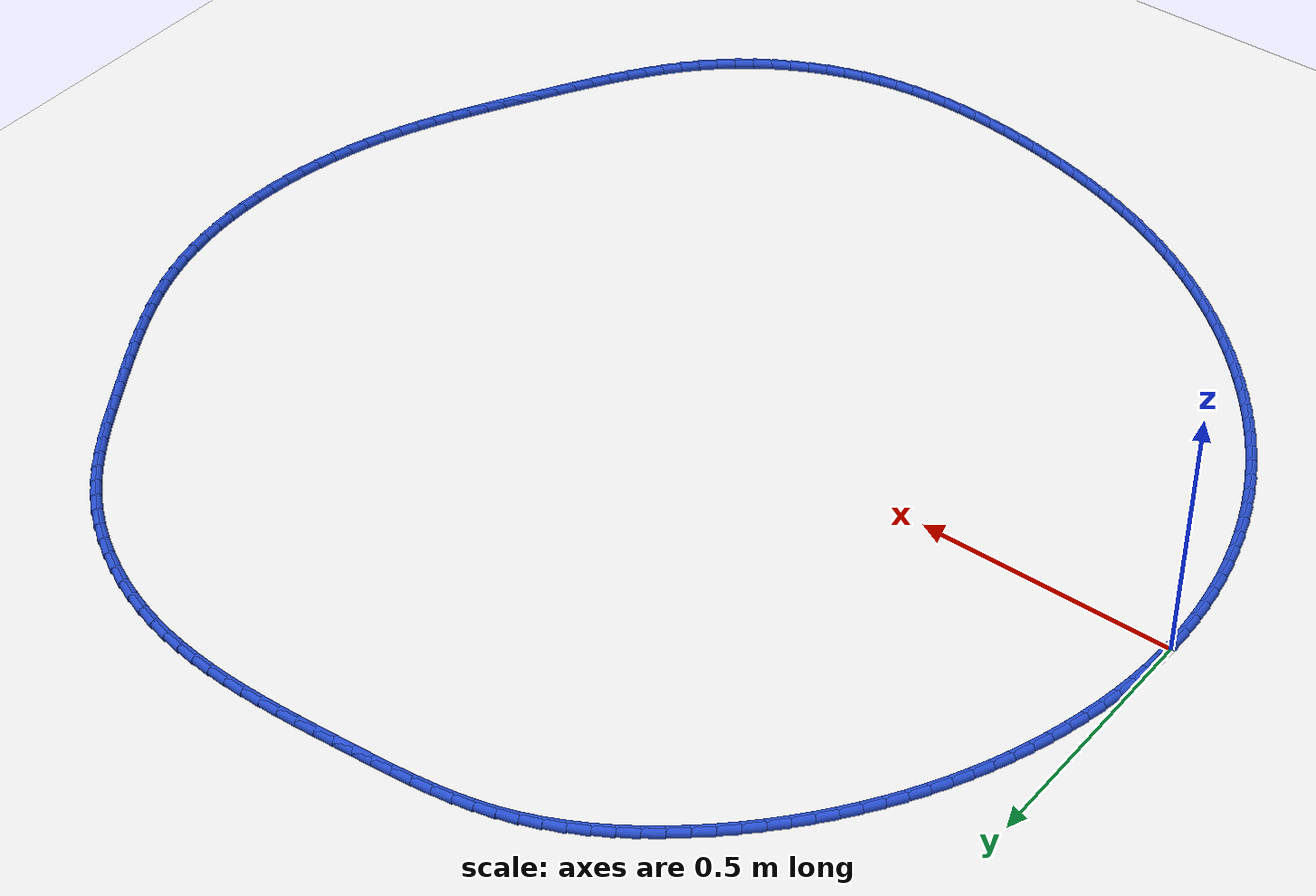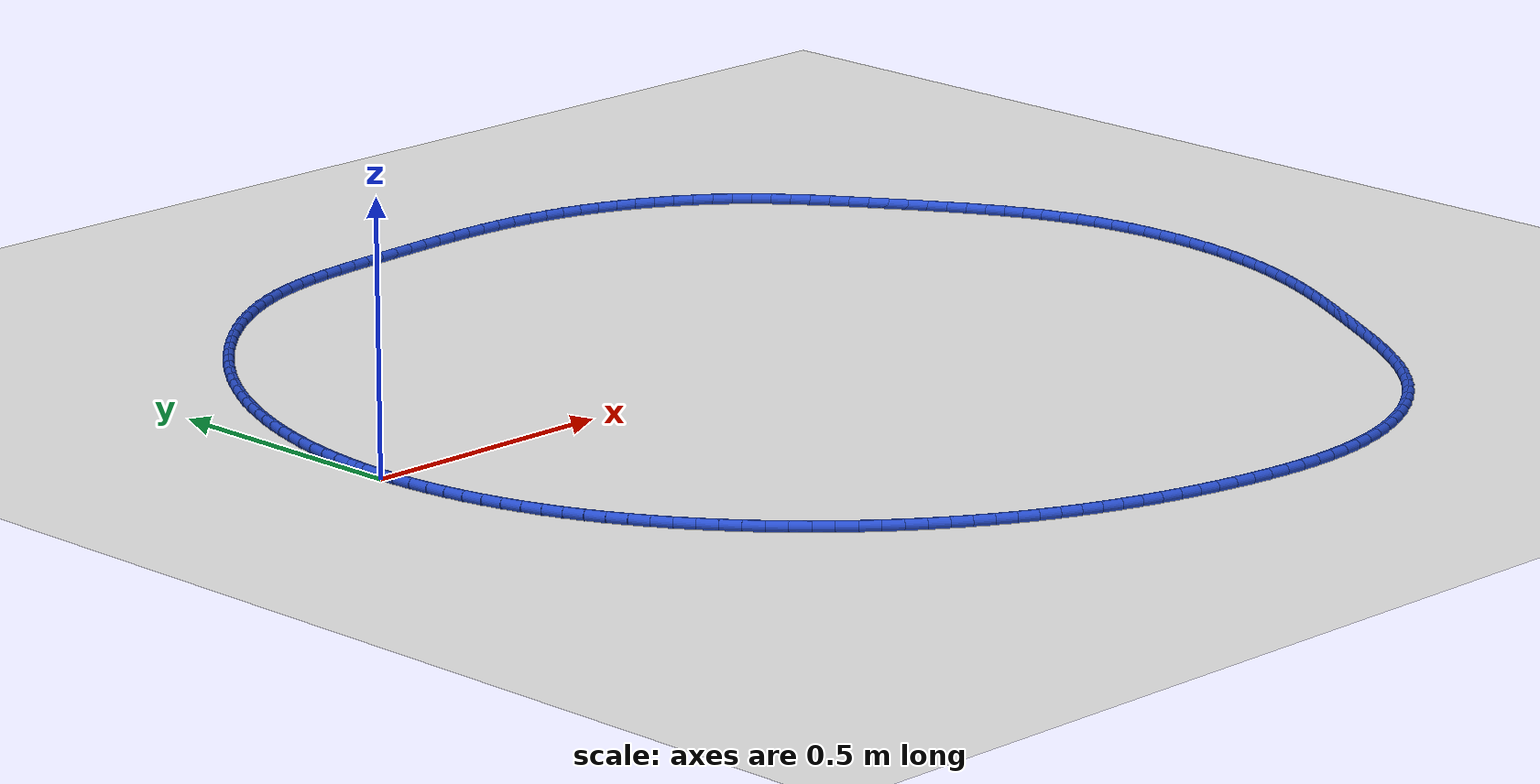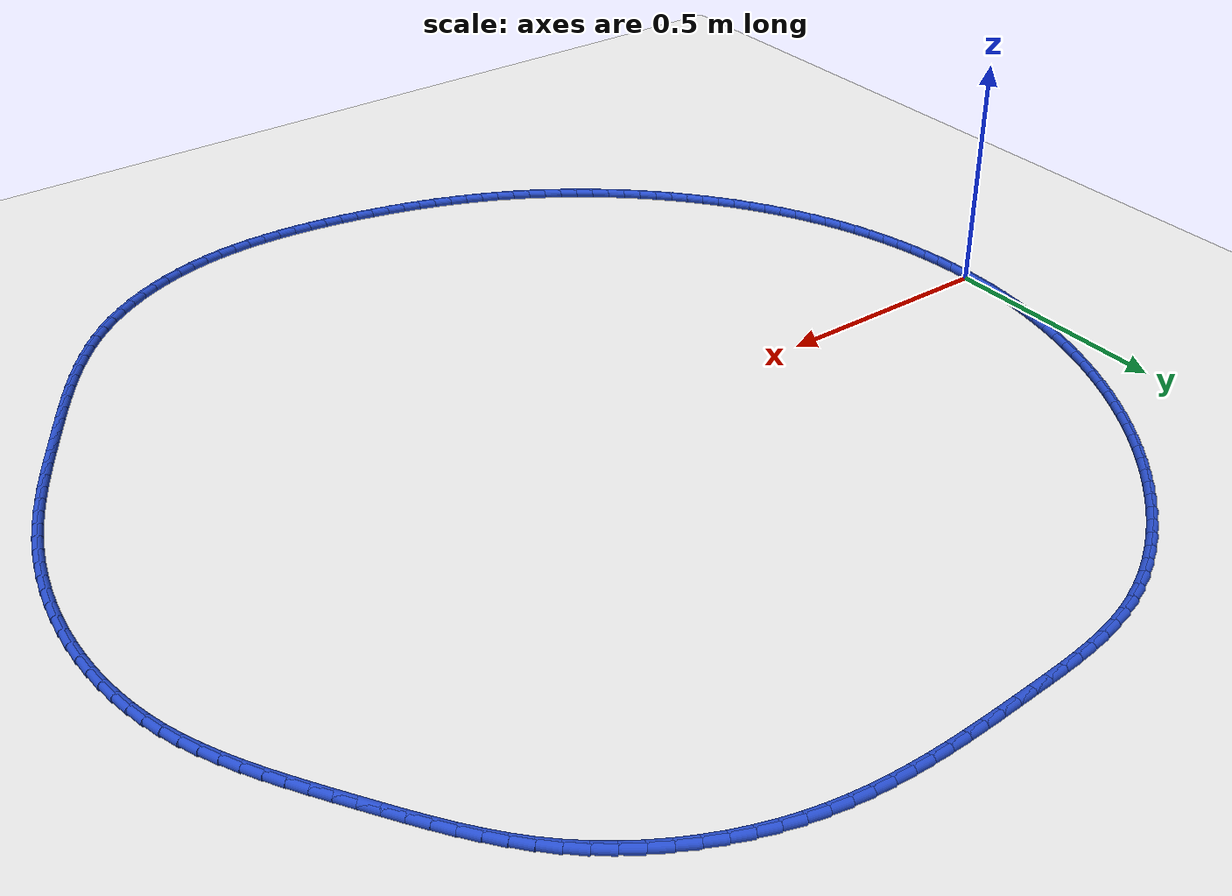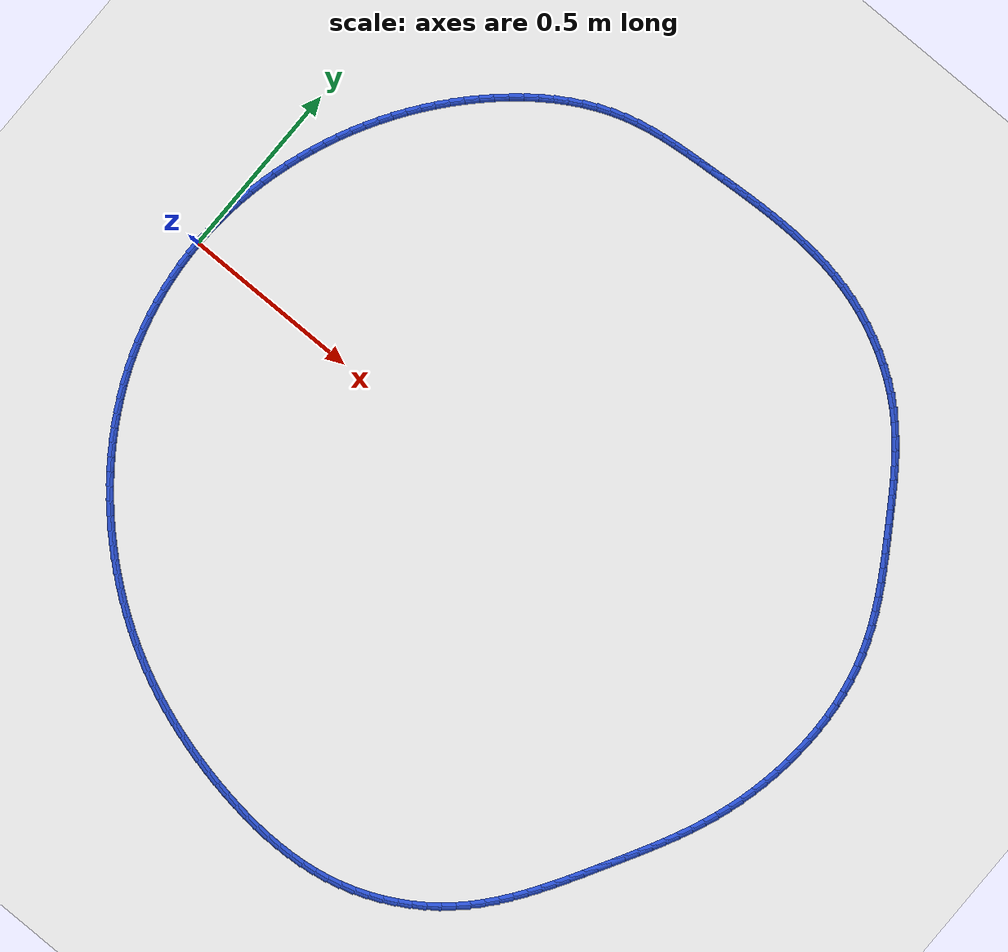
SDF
<sdf version="1.6">
 <world name="default">
  <light name="sun" type="directional">
   <pose>0 0 10 0 -0 0</pose>
   <diffuse>0.8 0.8 0.8 1</diffuse>
   <specular>0.2 0.2 0.2 1</specular>
   <attenuation>
    <range>1000</range>
    <constant>0.9</constant>
    <linear>0.01</linear>
    <quadratic>0.001</quadratic>
   </attenuation>
   <direction>-0.5 0.1 -0.9</direction>
  </light>
  <model name="ground_plane">
   <static>1</static>
   <link name="link">
    <collision name="collision">
     <geometry><plane><normal>0 0 1</normal><size>100 100</size></plane></geometry>
     <surface><friction><ode><mu>100</mu><mu2>50</mu2></ode></friction></surface>
    </collision>
    <visual name="visual">
     <cast_shadows>0</cast_shadows>
     <geometry><plane><normal>0 0 1</normal><size>100 100</size></plane></geometry>
     <material>
      <script><uri>file://media/materials/scripts/gazebo.material</uri><name>Gazebo/WhiteGlow</name></script>
     </material>
    </visual>
   </link>
  </model>
  <gravity>0 0 -9.8</gravity>
  <magnetic_field>6e-06 2.3e-05 -4.2e-05</magnetic_field>
  <atmosphere type="adiabatic"/>
  <physics name="default_physics" default="0" type="ode">
   <max_step_size>0.001</max_step_size>
   <real_time_factor>1</real_time_factor>
   <real_time_update_rate>1000</real_time_update_rate>
  </physics>
  <scene><ambient>0.4 0.4 0.4 1</ambient><background>0.7 0.7 0.7 1</background><shadows>1</shadows></scene>
  <spherical_coordinates>
   <surface_model>EARTH_WGS84</surface_model>
   <latitude_deg>0</latitude_deg>
   <longitude_deg>0</longitude_deg>
   <elevation>0</elevation>
   <heading_deg>0</heading_deg>
  </spherical_coordinates>
  <model name="line">
   <link name="link_0">
    <pose>-1.734723475976807e-17 -8.326672684688674e-17 0.01 0 1.57 1.5463397447681198</pose>
    <collision name="collision">
     <geometry><cylinder><radius>0.01</radius><length>0.08</length></cylinder></geometry>
    </collision>
    <visual name="visual">
     <material>
      <script><name>Gazebo/Blue</name><uri>file://media/materials/scripts/gazebo.material</uri></script>
     </material>
     <geometry><cylinder><radius>0.01</radius><length>0.08</length></cylinder></geometry>
    </visual>
   </link>
   <link name="link_1">
    <pose>0.0009439849745583349 0.03859070573324368 0.01 0 1.57 1.5070628620395163</pose>
    <collision name="collision">
     <geometry><cylinder><radius>0.01</radius><length>0.08</length></cylinder></geometry>
    </collision>
    <visual name="visual">
     <material>
      <script><name>Gazebo/Blue</name><uri>file://media/materials/scripts/gazebo.material</uri></script>
     </material>
     <geometry><cylinder><radius>0.01</radius><length>0.08</length></cylinder></geometry>
    </visual>
   </link>
   <link name="link_2">
    <pose>0.003401936481926688 0.07710457887876052 0.01 0 1.57 1.4685931180485814</pose>
    <collision name="collision">
     <geometry><cylinder><radius>0.01</radius><length>0.08</length></cylinder></geometry>
    </collision>
    <visual name="visual">
     <material>
      <script><name>Gazebo/Blue</name><uri>file://media/materials/scripts/gazebo.material</uri></script>
     </material>
     <geometry><cylinder><radius>0.01</radius><length>0.08</length></cylinder></geometry>
    </visual>
   </link>
   <link name="link_3">
    <pose>0.007339192734409644 0.11549415470578164 0.01 0 1.57 1.4308945284231824</pose>
    <collision name="collision">
     <geometry><cylinder><radius>0.01</radius><length>0.08</length></cylinder></geometry>
    </collision>
    <visual name="visual">
     <material>
      <script><name>Gazebo/Blue</name><uri>file://media/materials/scripts/gazebo.material</uri></script>
     </material>
     <geometry><cylinder><radius>0.01</radius><length>0.08</length></cylinder></geometry>
    </visual>
   </link>
   <link name="link_4">
    <pose>0.01272109194431181 0.1537119684835384 0.01 0 1.57 1.393923783328831</pose>
    <collision name="collision">
     <geometry><cylinder><radius>0.01</radius><length>0.08</length></cylinder></geometry>
    </collision>
    <visual name="visual">
     <material>
      <script><name>Gazebo/Blue</name><uri>file://media/materials/scripts/gazebo.material</uri></script>
     </material>
     <geometry><cylinder><radius>0.01</radius><length>0.08</length></cylinder></geometry>
    </visual>
   </link>
   <link name="link_5">
    <pose>0.019512972323937797 0.19171055548126217 0.01 0 1.57 1.3576313293015498</pose>
    <collision name="collision">
     <geometry><cylinder><radius>0.01</radius><length>0.08</length></cylinder></geometry>
    </collision>
    <visual name="visual">
     <material>
      <script><name>Gazebo/Blue</name><uri>file://media/materials/scripts/gazebo.material</uri></script>
     </material>
     <geometry><cylinder><radius>0.01</radius><length>0.08</length></cylinder></geometry>
    </visual>
   </link>
   <link name="link_6">
    <pose>0.027680172085592203 0.22944245096818425 0.01 0 1.57 1.3219623319104445</pose>
    <collision name="collision">
     <geometry><cylinder><radius>0.01</radius><length>0.08</length></cylinder></geometry>
    </collision>
    <visual name="visual">
     <material>
      <script><name>Gazebo/Blue</name><uri>file://media/materials/scripts/gazebo.material</uri></script>
     </material>
     <geometry><cylinder><radius>0.01</radius><length>0.08</length></cylinder></geometry>
    </visual>
   </link>
   <link name="link_7">
    <pose>0.03718802944157963 0.26686019021353585 0.01 0 1.57 1.2868575112122136</pose>
    <collision name="collision">
     <geometry><cylinder><radius>0.01</radius><length>0.08</length></cylinder></geometry>
    </collision>
    <visual name="visual">
     <material>
      <script><name>Gazebo/Blue</name><uri>file://media/materials/scripts/gazebo.material</uri></script>
     </material>
     <geometry><cylinder><radius>0.01</radius><length>0.08</length></cylinder></geometry>
    </visual>
   </link>
   <link name="link_8">
    <pose>0.04800188260420471 0.30391630848654844 0.01 0 1.57 1.2522538491054644</pose>
    <collision name="collision">
     <geometry><cylinder><radius>0.01</radius><length>0.08</length></cylinder></geometry>
    </collision>
    <visual name="visual">
     <material>
      <script><name>Gazebo/Blue</name><uri>file://media/materials/scripts/gazebo.material</uri></script>
     </material>
     <geometry><cylinder><radius>0.01</radius><length>0.08</length></cylinder></geometry>
    </visual>
   </link>
   <link name="link_9">
    <pose>0.06008706978577201 0.34056334105645314 0.01 0 1.57 1.2180800754891843</pose>
    <collision name="collision">
     <geometry><cylinder><radius>0.01</radius><length>0.08</length></cylinder></geometry>
    </collision>
    <visual name="visual">
     <material>
      <script><name>Gazebo/Blue</name><uri>file://media/materials/scripts/gazebo.material</uri></script>
     </material>
     <geometry><cylinder><radius>0.01</radius><length>0.08</length></cylinder></geometry>
    </visual>
   </link>
   <link name="link_10">
    <pose>0.07340922310923467 0.3767540525552776 0.01 0 1.57 1.1841103861748596</pose>
    <collision name="collision">
     <geometry><cylinder><radius>0.01</radius><length>0.08</length></cylinder></geometry>
    </collision>
    <visual name="visual">
     <material>
      <script><name>Gazebo/Blue</name><uri>file://media/materials/scripts/gazebo.material</uri></script>
     </material>
     <geometry><cylinder><radius>0.01</radius><length>0.08</length></cylinder></geometry>
    </visual>
   </link>
   <link name="link_11">
    <pose>0.08794359539578611 0.4124487154418657 0.01 0 1.57 1.1501239313518643</pose>
    <collision name="collision">
     <geometry><cylinder><radius>0.01</radius><length>0.08</length></cylinder></geometry>
    </collision>
    <visual name="visual">
     <material>
      <script><name>Gazebo/Blue</name><uri>file://media/materials/scripts/gazebo.material</uri></script>
     </material>
     <geometry><cylinder><radius>0.01</radius><length>0.08</length></cylinder></geometry>
    </visual>
   </link>
   <link name="link_12">
    <pose>0.1036769828693089 0.447616610447237 0.01 0 1.57 1.1161009046123511</pose>
    <collision name="collision">
     <geometry><cylinder><radius>0.01</radius><length>0.08</length></cylinder></geometry>
    </collision>
    <visual name="visual">
     <material>
      <script><name>Gazebo/Blue</name><uri>file://media/materials/scripts/gazebo.material</uri></script>
     </material>
     <geometry><cylinder><radius>0.01</radius><length>0.08</length></cylinder></geometry>
    </visual>
   </link>
   <link name="link_13">
    <pose>0.120596864211239 0.48222755088050373 0.01 0 1.57 1.0820335895706508</pose>
    <collision name="collision">
     <geometry><cylinder><radius>0.01</radius><length>0.08</length></cylinder></geometry>
    </collision>
    <visual name="visual">
     <material>
      <script><name>Gazebo/Blue</name><uri>file://media/materials/scripts/gazebo.material</uri></script>
     </material>
     <geometry><cylinder><radius>0.01</radius><length>0.08</length></cylinder></geometry>
    </visual>
   </link>
   <link name="link_14">
    <pose>0.13869071810301242 0.5162513500507782 0.01 0 1.57 1.0479147006054637</pose>
    <collision name="collision">
     <geometry><cylinder><radius>0.01</radius><length>0.08</length></cylinder></geometry>
    </collision>
    <visual name="visual">
     <material>
      <script><name>Gazebo/Blue</name><uri>file://media/materials/scripts/gazebo.material</uri></script>
     </material>
     <geometry><cylinder><radius>0.01</radius><length>0.08</length></cylinder></geometry>
    </visual>
   </link>
   <link name="link_15">
    <pose>0.1579460232260652 0.5496578212671728 0.01 0 1.57 1.0137375584918418</pose>
    <collision name="collision">
     <geometry><cylinder><radius>0.01</radius><length>0.08</length></cylinder></geometry>
    </collision>
    <visual name="visual">
     <material>
      <script><name>Gazebo/Blue</name><uri>file://media/materials/scripts/gazebo.material</uri></script>
     </material>
     <geometry><cylinder><radius>0.01</radius><length>0.08</length></cylinder></geometry>
    </visual>
   </link>
   <link name="link_16">
    <pose>0.1783502582618334 0.5824167778388 0.01 0 1.57 0.9794962635091228</pose>
    <collision name="collision">
     <geometry><cylinder><radius>0.01</radius><length>0.08</length></cylinder></geometry>
    </collision>
    <visual name="visual">
     <material>
      <script><name>Gazebo/Blue</name><uri>file://media/materials/scripts/gazebo.material</uri></script>
     </material>
     <geometry><cylinder><radius>0.01</radius><length>0.08</length></cylinder></geometry>
    </visual>
   </link>
   <link name="link_17">
    <pose>0.1998909018917531 0.6144980330747718 0.01 0 1.57 0.9451858645704128</pose>
    <collision name="collision">
     <geometry><cylinder><radius>0.01</radius><length>0.08</length></cylinder></geometry>
    </collision>
    <visual name="visual">
     <material>
      <script><name>Gazebo/Blue</name><uri>file://media/materials/scripts/gazebo.material</uri></script>
     </material>
     <geometry><cylinder><radius>0.01</radius><length>0.08</length></cylinder></geometry>
    </visual>
   </link>
   <link name="link_18">
    <pose>0.22255543279726006 0.6458714002842006 0.01 0 1.57 0.9108025227620948</pose>
    <collision name="collision">
     <geometry><cylinder><radius>0.01</radius><length>0.08</length></cylinder></geometry>
    </collision>
    <visual name="visual">
     <material>
      <script><name>Gazebo/Blue</name><uri>file://media/materials/scripts/gazebo.material</uri></script>
     </material>
     <geometry><cylinder><radius>0.01</radius><length>0.08</length></cylinder></geometry>
    </visual>
   </link>
   <link name="link_19">
    <pose>0.2463313296597906 0.676506692776199 0.01 0 1.57 0.876343667512497</pose>
    <collision name="collision">
     <geometry><cylinder><radius>0.01</radius><length>0.08</length></cylinder></geometry>
    </collision>
    <visual name="visual">
     <material>
      <script><name>Gazebo/Blue</name><uri>file://media/materials/scripts/gazebo.material</uri></script>
     </material>
     <geometry><cylinder><radius>0.01</radius><length>0.08</length></cylinder></geometry>
    </visual>
   </link>
   <link name="link_20">
    <pose>0.27120607116078066 0.7063737238598793 0.01 0 1.57 0.8418081434369663</pose>
    <collision name="collision">
     <geometry><cylinder><radius>0.01</radius><length>0.08</length></cylinder></geometry>
    </collision>
    <visual name="visual">
     <material>
      <script><name>Gazebo/Blue</name><uri>file://media/materials/scripts/gazebo.material</uri></script>
     </material>
     <geometry><cylinder><radius>0.01</radius><length>0.08</length></cylinder></geometry>
    </visual>
   </link>
   <link name="link_21">
    <pose>0.2971671359816662 0.7354423068443537 0.01 0 1.57 0.8071945859510348</pose>
    <collision name="collision">
     <geometry><cylinder><radius>0.01</radius><length>0.08</length></cylinder></geometry>
    </collision>
    <visual name="visual">
     <material>
      <script><name>Gazebo/Blue</name><uri>file://media/materials/scripts/gazebo.material</uri></script>
     </material>
     <geometry><cylinder><radius>0.01</radius><length>0.08</length></cylinder></geometry>
    </visual>
   </link>
   <link name="link_22">
    <pose>0.32420197836281417 0.76368213002093 0.01 0 1.57 0.7720100453775888</pose>
    <collision name="collision">
     <geometry><cylinder><radius>0.01</radius><length>0.08</length></cylinder></geometry>
    </collision>
    <visual name="visual">
     <material>
      <script><name>Gazebo/Blue</name><uri>file://media/materials/scripts/gazebo.material</uri></script>
     </material>
     <geometry><cylinder><radius>0.01</radius><length>0.08</length></cylinder></geometry>
    </visual>
   </link>
   <link name="link_23">
    <pose>0.3522915115611468 0.7910294240859487 0.01 0 1.57 0.7349702492018789</pose>
    <collision name="collision">
     <geometry><cylinder><radius>0.01</radius><length>0.08</length></cylinder></geometry>
    </collision>
    <visual name="visual">
     <material>
      <script><name>Gazebo/Blue</name><uri>file://media/materials/scripts/gazebo.material</uri></script>
     </material>
     <geometry><cylinder><radius>0.01</radius><length>0.08</length></cylinder></geometry>
    </visual>
   </link>
   <link name="link_24">
    <pose>0.3814013230637737 0.8173420273344748 0.01 0 1.57 0.6956521147277249</pose>
    <collision name="collision">
     <geometry><cylinder><radius>0.01</radius><length>0.08</length></cylinder></geometry>
    </collision>
    <visual name="visual">
     <material>
      <script><name>Gazebo/Blue</name><uri>file://media/materials/scripts/gazebo.material</uri></script>
     </material>
     <geometry><cylinder><radius>0.01</radius><length>0.08</length></cylinder></geometry>
    </visual>
   </link>
   <link name="link_25">
    <pose>0.4114948082788859 0.8424665654221875 0.01 0 1.57 0.6537852112680071</pose>
    <collision name="collision">
     <geometry><cylinder><radius>0.01</radius><length>0.08</length></cylinder></geometry>
    </collision>
    <visual name="visual">
     <material>
      <script><name>Gazebo/Blue</name><uri>file://media/materials/scripts/gazebo.material</uri></script>
     </material>
     <geometry><cylinder><radius>0.01</radius><length>0.08</length></cylinder></geometry>
    </visual>
   </link>
   <link name="link_26">
    <pose>0.442535362614675 0.8662496640047664 0.01 0 1.57 0.6090977032960706</pose>
    <collision name="collision">
     <geometry><cylinder><radius>0.01</radius><length>0.08</length></cylinder></geometry>
    </collision>
    <visual name="visual">
     <material>
      <script><name>Gazebo/Blue</name><uri>file://media/materials/scripts/gazebo.material</uri></script>
     </material>
     <geometry><cylinder><radius>0.01</radius><length>0.08</length></cylinder></geometry>
    </visual>
   </link>
   <link name="link_27">
    <pose>0.4744863814793317 0.888537948737891 0.01 0 1.57 0.5613231457653641</pose>
    <collision name="collision">
     <geometry><cylinder><radius>0.01</radius><length>0.08</length></cylinder></geometry>
    </collision>
    <visual name="visual">
     <material>
      <script><name>Gazebo/Blue</name><uri>file://media/materials/scripts/gazebo.material</uri></script>
     </material>
     <geometry><cylinder><radius>0.01</radius><length>0.08</length></cylinder></geometry>
    </visual>
   </link>
   <link name="link_28">
    <pose>0.5073112602810474 0.9091780452772408 0.01 0 1.57 0.5102109944881843</pose>
    <collision name="collision">
     <geometry><cylinder><radius>0.01</radius><length>0.08</length></cylinder></geometry>
    </collision>
    <visual name="visual">
     <material>
      <script><name>Gazebo/Blue</name><uri>file://media/materials/scripts/gazebo.material</uri></script>
     </material>
     <geometry><cylinder><radius>0.01</radius><length>0.08</length></cylinder></geometry>
    </visual>
   </link>
   <link name="link_29">
    <pose>0.5409733944280133 0.9280165792784953 0.01 0 1.57 0.4555415353464049</pose>
    <collision name="collision">
     <geometry><cylinder><radius>0.01</radius><length>0.08</length></cylinder></geometry>
    </collision>
    <visual name="visual">
     <material>
      <script><name>Gazebo/Blue</name><uri>file://media/materials/scripts/gazebo.material</uri></script>
     </material>
     <geometry><cylinder><radius>0.01</radius><length>0.08</length></cylinder></geometry>
    </visual>
   </link>
   <link name="link_30">
    <pose>0.5754361793284204 0.9449001763973337 0.01 0 1.57 0.3971456847346548</pose>
    <collision name="collision">
     <geometry><cylinder><radius>0.01</radius><length>0.08</length></cylinder></geometry>
    </collision>
    <visual name="visual">
     <material>
      <script><name>Gazebo/Blue</name><uri>file://media/materials/scripts/gazebo.material</uri></script>
     </material>
     <geometry><cylinder><radius>0.01</radius><length>0.08</length></cylinder></geometry>
    </visual>
   </link>
   <link name="link_31">
    <pose>0.61066301039046 0.9596754622894359 0.01 0 1.57 0.3349297929277181</pose>
    <collision name="collision">
     <geometry><cylinder><radius>0.01</radius><length>0.08</length></cylinder></geometry>
    </collision>
    <visual name="visual">
     <material>
      <script><name>Gazebo/Blue</name><uri>file://media/materials/scripts/gazebo.material</uri></script>
     </material>
     <geometry><cylinder><radius>0.01</radius><length>0.08</length></cylinder></geometry>
    </visual>
   </link>
   <link name="link_32">
    <pose>0.6466172818232039 0.9721890732607043 0.01 0 1.57 0.2713595152694135</pose>
    <collision name="collision">
     <geometry><cylinder><radius>0.01</radius><length>0.08</length></cylinder></geometry>
    </collision>
    <visual name="visual">
     <material>
      <script><name>Gazebo/Blue</name><uri>file://media/materials/scripts/gazebo.material</uri></script>
     </material>
     <geometry><cylinder><radius>0.01</radius><length>0.08</length></cylinder></geometry>
    </visual>
   </link>
   <link name="link_33">
    <pose>0.683251807551593 0.9823816165549838 0.01 0 1.57 0.21511644359591622</pose>
    <collision name="collision">
     <geometry><cylinder><radius>0.01</radius><length>0.08</length></cylinder></geometry>
    </collision>
    <visual name="visual">
     <material>
      <script><name>Gazebo/Blue</name><uri>file://media/materials/scripts/gazebo.material</uri></script>
     </material>
     <geometry><cylinder><radius>0.01</radius><length>0.08</length></cylinder></geometry>
    </visual>
   </link>
   <link name="link_34">
    <pose>0.7204830525690591 0.9905165398186103 0.01 0 1.57 0.16825621912814284</pose>
    <collision name="collision">
     <geometry><cylinder><radius>0.01</radius><length>0.08</length></cylinder></geometry>
    </collision>
    <visual name="visual">
     <material>
      <script><name>Gazebo/Blue</name><uri>file://media/materials/scripts/gazebo.material</uri></script>
     </material>
     <geometry><cylinder><radius>0.01</radius><length>0.08</length></cylinder></geometry>
    </visual>
   </link>
   <link name="link_35">
    <pose>0.7582196820349184 0.9969265665054989 0.01 0 1.57 0.1307765694079937</pose>
    <collision name="collision">
     <geometry><cylinder><radius>0.01</radius><length>0.08</length></cylinder></geometry>
    </collision>
    <visual name="visual">
     <material>
      <script><name>Gazebo/Blue</name><uri>file://media/materials/scripts/gazebo.material</uri></script>
     </material>
     <geometry><cylinder><radius>0.01</radius><length>0.08</length></cylinder></geometry>
    </visual>
   </link>
   <link name="link_36">
    <pose>0.7963703611084877 1.0019444200695669 0.01 0 1.57 0.10252603342590993</pose>
    <collision name="collision">
     <geometry><cylinder><radius>0.01</radius><length>0.08</length></cylinder></geometry>
    </collision>
    <visual name="visual">
     <material>
      <script><name>Gazebo/Blue</name><uri>file://media/materials/scripts/gazebo.material</uri></script>
     </material>
     <geometry><cylinder><radius>0.01</radius><length>0.08</length></cylinder></geometry>
    </visual>
   </link>
   <link name="link_37">
    <pose>0.8348437549490839 1.0059028239647307 0.01 0 1.57 0.08330236118696152</pose>
    <collision name="collision">
     <geometry><cylinder><radius>0.01</radius><length>0.08</length></cylinder></geometry>
    </collision>
    <visual name="visual">
     <material>
      <script><name>Gazebo/Blue</name><uri>file://media/materials/scripts/gazebo.material</uri></script>
     </material>
     <geometry><cylinder><radius>0.01</radius><length>0.08</length></cylinder></geometry>
    </visual>
   </link>
   <link name="link_38">
    <pose>0.8735485287160228 1.0091345016449063 0.01 0 1.57 0.07292203499505044</pose>
    <collision name="collision">
     <geometry><cylinder><radius>0.01</radius><length>0.08</length></cylinder></geometry>
    </collision>
    <visual name="visual">
     <material>
      <script><name>Gazebo/Blue</name><uri>file://media/materials/scripts/gazebo.material</uri></script>
     </material>
     <geometry><cylinder><radius>0.01</radius><length>0.08</length></cylinder></geometry>
    </visual>
   </link>
   <link name="link_39">
    <pose>0.912393347568622 1.011972176564011 0.01 0 1.57 0.07037023695720648</pose>
    <collision name="collision">
     <geometry><cylinder><radius>0.01</radius><length>0.08</length></cylinder></geometry>
    </collision>
    <visual name="visual">
     <material>
      <script><name>Gazebo/Blue</name><uri>file://media/materials/scripts/gazebo.material</uri></script>
     </material>
     <geometry><cylinder><radius>0.01</radius><length>0.08</length></cylinder></geometry>
    </visual>
   </link>
   <link name="link_40">
    <pose>0.9512912632057258 1.0147139593415782 0.01 0 1.57 0.06763601080576731</pose>
    <collision name="collision">
     <geometry><cylinder><radius>0.01</radius><length>0.08</length></cylinder></geometry>
    </collision>
    <visual name="visual">
     <material>
      <script><name>Gazebo/Blue</name><uri>file://media/materials/scripts/gazebo.material</uri></script>
     </material>
     <geometry><cylinder><radius>0.01</radius><length>0.08</length></cylinder></geometry>
    </visual>
   </link>
   <link name="link_41">
    <pose>0.9901944525393018 1.0173492355729898 0.01 0 1.57 0.06052017866593311</pose>
    <collision name="collision">
     <geometry><cylinder><radius>0.01</radius><length>0.08</length></cylinder></geometry>
    </collision>
    <visual name="visual">
     <material>
      <script><name>Gazebo/Blue</name><uri>file://media/materials/scripts/gazebo.material</uri></script>
     </material>
     <geometry><cylinder><radius>0.01</radius><length>0.08</length></cylinder></geometry>
    </visual>
   </link>
   <link name="link_42">
    <pose>1.0290756459881667 1.01970520945211 0.01 0 1.57 0.048952177614966064</pose>
    <collision name="collision">
     <geometry><cylinder><radius>0.01</radius><length>0.08</length></cylinder></geometry>
    </collision>
    <visual name="visual">
     <material>
      <script><name>Gazebo/Blue</name><uri>file://media/materials/scripts/gazebo.material</uri></script>
     </material>
     <geometry><cylinder><radius>0.01</radius><length>0.08</length></cylinder></geometry>
    </visual>
   </link>
   <link name="link_43">
    <pose>1.0679077564011572 1.0216076456736218 0.01 0 1.57 0.03287764250212933</pose>
    <collision name="collision">
     <geometry><cylinder><radius>0.01</radius><length>0.08</length></cylinder></geometry>
    </collision>
    <visual name="visual">
     <material>
      <script><name>Gazebo/Blue</name><uri>file://media/materials/scripts/gazebo.material</uri></script>
     </material>
     <geometry><cylinder><radius>0.01</radius><length>0.08</length></cylinder></geometry>
    </visual>
   </link>
   <link name="link_44">
    <pose>1.10666369662711 1.0228823089322074 0.01 0 1.57 0.012227648856373572</pose>
    <collision name="collision">
     <geometry><cylinder><radius>0.01</radius><length>0.08</length></cylinder></geometry>
    </collision>
    <visual name="visual">
     <material>
      <script><name>Gazebo/Blue</name><uri>file://media/materials/scripts/gazebo.material</uri></script>
     </material>
     <geometry><cylinder><radius>0.01</radius><length>0.08</length></cylinder></geometry>
    </visual>
   </link>
   <link name="link_45">
    <pose>1.145316379514862 1.0233549639225499 0.01 0 1.57 -0.013071893357528013</pose>
    <collision name="collision">
     <geometry><cylinder><radius>0.01</radius><length>0.08</length></cylinder></geometry>
    </collision>
    <visual name="visual">
     <material>
      <script><name>Gazebo/Blue</name><uri>file://media/materials/scripts/gazebo.material</uri></script>
     </material>
     <geometry><cylinder><radius>0.01</radius><length>0.08</length></cylinder></geometry>
    </visual>
   </link>
   <link name="link_46">
    <pose>1.1838387179132503 1.0228513753393318 0.01 0 1.57 -0.043087390800113444</pose>
    <collision name="collision">
     <geometry><cylinder><radius>0.01</radius><length>0.08</length></cylinder></geometry>
    </collision>
    <visual name="visual">
     <material>
      <script><name>Gazebo/Blue</name><uri>file://media/materials/scripts/gazebo.material</uri></script>
     </material>
     <geometry><cylinder><radius>0.01</radius><length>0.08</length></cylinder></geometry>
    </visual>
   </link>
   <link name="link_47">
    <pose>1.2222036246711114 1.0211973078772358 0.01 0 1.57 -0.07786091044570956</pose>
    <collision name="collision">
     <geometry><cylinder><radius>0.01</radius><length>0.08</length></cylinder></geometry>
    </collision>
    <visual name="visual">
     <material>
      <script><name>Gazebo/Blue</name><uri>file://media/materials/scripts/gazebo.material</uri></script>
     </material>
     <geometry><cylinder><radius>0.01</radius><length>0.08</length></cylinder></geometry>
    </visual>
   </link>
   <link name="link_48">
    <pose>1.2603840126372823 1.0182185262309447 0.01 0 1.57 -0.11738970162927613</pose>
    <collision name="collision">
     <geometry><cylinder><radius>0.01</radius><length>0.08</length></cylinder></geometry>
    </collision>
    <visual name="visual">
     <material>
      <script><name>Gazebo/Blue</name><uri>file://media/materials/scripts/gazebo.material</uri></script>
     </material>
     <geometry><cylinder><radius>0.01</radius><length>0.08</length></cylinder></geometry>
    </visual>
   </link>
   <link name="link_49">
    <pose>1.2983527946605993 1.0137407950951403 0.01 0 1.57 -0.16160253391109483</pose>
    <collision name="collision">
     <geometry><cylinder><radius>0.01</radius><length>0.08</length></cylinder></geometry>
    </collision>
    <visual name="visual">
     <material>
      <script><name>Gazebo/Blue</name><uri>file://media/materials/scripts/gazebo.material</uri></script>
     </material>
     <geometry><cylinder><radius>0.01</radius><length>0.08</length></cylinder></geometry>
    </visual>
   </link>
   <link name="link_50">
    <pose>1.3360828835898995 1.007589879164506 0.01 0 1.57 -0.21033449076955885</pose>
    <collision name="collision">
     <geometry><cylinder><radius>0.01</radius><length>0.08</length></cylinder></geometry>
    </collision>
    <visual name="visual">
     <material>
      <script><name>Gazebo/Blue</name><uri>file://media/materials/scripts/gazebo.material</uri></script>
     </material>
     <geometry><cylinder><radius>0.01</radius><length>0.08</length></cylinder></geometry>
    </visual>
   </link>
   <link name="link_51">
    <pose>1.3735471922740197 0.9995915431337246 0.01 0 1.57 -0.26317317947111213</pose>
    <collision name="collision">
     <geometry><cylinder><radius>0.01</radius><length>0.08</length></cylinder></geometry>
    </collision>
    <visual name="visual">
     <material>
      <script><name>Gazebo/Blue</name><uri>file://media/materials/scripts/gazebo.material</uri></script>
     </material>
     <geometry><cylinder><radius>0.01</radius><length>0.08</length></cylinder></geometry>
    </visual>
   </link>
   <link name="link_52">
    <pose>1.410715014947106 0.9895777080278719 0.01 0 1.57 -0.3174085424207179</pose>
    <collision name="collision">
     <geometry><cylinder><radius>0.01</radius><length>0.08</length></cylinder></geometry>
    </collision>
    <visual name="visual">
     <material>
      <script><name>Gazebo/Blue</name><uri>file://media/materials/scripts/gazebo.material</uri></script>
     </material>
     <geometry><cylinder><radius>0.01</radius><length>0.08</length></cylinder></geometry>
    </visual>
   </link>
   <link name="link_53">
    <pose>1.4474866739502357 0.9774976363957565 0.01 0 1.57 -0.37109705965039824</pose>
    <collision name="collision">
     <geometry><cylinder><radius>0.01</radius><length>0.08</length></cylinder></geometry>
    </collision>
    <visual name="visual">
     <material>
      <script><name>Gazebo/Blue</name><uri>file://media/materials/scripts/gazebo.material</uri></script>
     </material>
     <geometry><cylinder><radius>0.01</radius><length>0.08</length></cylinder></geometry>
    </visual>
   </link>
   <link name="link_54">
    <pose>1.4837006176620018 0.9634058566374532 0.01 0 1.57 -0.4245772907462162</pose>
    <collision name="collision">
     <geometry><cylinder><radius>0.01</radius><length>0.08</length></cylinder></geometry>
    </collision>
    <visual name="visual">
     <material>
      <script><name>Gazebo/Blue</name><uri>file://media/materials/scripts/gazebo.material</uri></script>
     </material>
     <geometry><cylinder><radius>0.01</radius><length>0.08</length></cylinder></geometry>
    </visual>
   </link>
   <link name="link_55">
    <pose>1.51919310068289 0.9473606294163424 0.01 0 1.57 -0.4782590592508051</pose>
    <collision name="collision">
     <geometry><cylinder><radius>0.01</radius><length>0.08</length></cylinder></geometry>
    </collision>
    <visual name="visual">
     <material>
      <script><name>Gazebo/Blue</name><uri>file://media/materials/scripts/gazebo.material</uri></script>
     </material>
     <geometry><cylinder><radius>0.01</radius><length>0.08</length></cylinder></geometry>
    </visual>
   </link>
   <link name="link_56">
    <pose>1.5538003776133873 0.9294202153958064 0.01 0 1.57 -0.5325460859215124</pose>
    <collision name="collision">
     <geometry><cylinder><radius>0.01</radius><length>0.08</length></cylinder></geometry>
    </collision>
    <visual name="visual">
     <material>
      <script><name>Gazebo/Blue</name><uri>file://media/materials/scripts/gazebo.material</uri></script>
     </material>
     <geometry><cylinder><radius>0.01</radius><length>0.08</length></cylinder></geometry>
    </visual>
   </link>
   <link name="link_57">
    <pose>1.5873587030539802 0.9096428752392258 0.01 0 1.57 -0.5878367783793388</pose>
    <collision name="collision">
     <geometry><cylinder><radius>0.01</radius><length>0.08</length></cylinder></geometry>
    </collision>
    <visual name="visual">
     <material>
      <script><name>Gazebo/Blue</name><uri>file://media/materials/scripts/gazebo.material</uri></script>
     </material>
     <geometry><cylinder><radius>0.01</radius><length>0.08</length></cylinder></geometry>
    </visual>
   </link>
   <link name="link_58">
    <pose>1.6197043316051563 0.888086869609982 0.01 0 1.57 -0.6445237044924059</pose>
    <collision name="collision">
     <geometry><cylinder><radius>0.01</radius><length>0.08</length></cylinder></geometry>
    </collision>
    <visual name="visual">
     <material>
      <script><name>Gazebo/Blue</name><uri>file://media/materials/scripts/gazebo.material</uri></script>
     </material>
     <geometry><cylinder><radius>0.01</radius><length>0.08</length></cylinder></geometry>
    </visual>
   </link>
   <link name="link_59">
    <pose>1.6506735178674006 0.8648104591714563 0.01 0 1.57 -0.7029910225501479</pose>
    <collision name="collision">
     <geometry><cylinder><radius>0.01</radius><length>0.08</length></cylinder></geometry>
    </collision>
    <visual name="visual">
     <material>
      <script><name>Gazebo/Blue</name><uri>file://media/materials/scripts/gazebo.material</uri></script>
     </material>
     <geometry><cylinder><radius>0.01</radius><length>0.08</length></cylinder></geometry>
    </visual>
   </link>
   <link name="link_60">
    <pose>1.6801025164411998 0.8398719045870299 0.01 0 1.57 -0.7633550163235864</pose>
    <collision name="collision">
     <geometry><cylinder><radius>0.01</radius><length>0.08</length></cylinder></geometry>
    </collision>
    <visual name="visual">
     <material>
      <script><name>Gazebo/Blue</name><uri>file://media/materials/scripts/gazebo.material</uri></script>
     </material>
     <geometry><cylinder><radius>0.01</radius><length>0.08</length></cylinder></geometry>
    </visual>
   </link>
   <link name="link_61">
    <pose>1.7078377859886962 0.8133331980856022 0.01 0 1.57 -0.8207569188890868</pose>
    <collision name="collision">
     <geometry><cylinder><radius>0.01</radius><length>0.08</length></cylinder></geometry>
    </collision>
    <visual name="visual">
     <material>
      <script><name>Gazebo/Blue</name><uri>file://media/materials/scripts/gazebo.material</uri></script>
     </material>
     <geometry><cylinder><radius>0.01</radius><length>0.08</length></cylinder></geometry>
    </visual>
   </link>
   <link name="link_62">
    <pose>1.7339274525710753 0.7853300804814889 0.01 0 1.57 -0.8702334164334655</pose>
    <collision name="collision">
     <geometry><cylinder><radius>0.01</radius><length>0.08</length></cylinder></geometry>
    </collision>
    <visual name="visual">
     <material>
      <script><name>Gazebo/Blue</name><uri>file://media/materials/scripts/gazebo.material</uri></script>
     </material>
     <geometry><cylinder><radius>0.01</radius><length>0.08</length></cylinder></geometry>
    </visual>
   </link>
   <link name="link_63">
    <pose>1.7586045077514432 0.7560658968191533 0.01 0 1.57 -0.911347549807617</pose>
    <collision name="collision">
     <geometry><cylinder><radius>0.01</radius><length>0.08</length></cylinder></geometry>
    </collision>
    <visual name="visual">
     <material>
      <script><name>Gazebo/Blue</name><uri>file://media/materials/scripts/gazebo.material</uri></script>
     </material>
     <geometry><cylinder><radius>0.01</radius><length>0.08</length></cylinder></geometry>
    </visual>
   </link>
   <link name="link_64">
    <pose>1.782108778801453 0.7257464919215956 0.01 0 1.57 -0.9440362224663276</pose>
    <collision name="collision">
     <geometry><cylinder><radius>0.01</radius><length>0.08</length></cylinder></geometry>
    </collision>
    <visual name="visual">
     <material>
      <script><name>Gazebo/Blue</name><uri>file://media/materials/scripts/gazebo.material</uri></script>
     </material>
     <geometry><cylinder><radius>0.01</radius><length>0.08</length></cylinder></geometry>
    </visual>
   </link>
   <link name="link_65">
    <pose>1.804680092992756 0.6945777106118158 0.01 0 1.57 -0.9683548944947087</pose>
    <collision name="collision">
     <geometry><cylinder><radius>0.01</radius><length>0.08</length></cylinder></geometry>
    </collision>
    <visual name="visual">
     <material>
      <script><name>Gazebo/Blue</name><uri>file://media/materials/scripts/gazebo.material</uri></script>
     </material>
     <geometry><cylinder><radius>0.01</radius><length>0.08</length></cylinder></geometry>
    </visual>
   </link>
   <link name="link_66">
    <pose>1.8265582775970062 0.6627653977128141 0.01 0 1.57 -0.9844079972430734</pose>
    <collision name="collision">
     <geometry><cylinder><radius>0.01</radius><length>0.08</length></cylinder></geometry>
    </collision>
    <visual name="visual">
     <material>
      <script><name>Gazebo/Blue</name><uri>file://media/materials/scripts/gazebo.material</uri></script>
     </material>
     <geometry><cylinder><radius>0.01</radius><length>0.08</length></cylinder></geometry>
    </visual>
   </link>
   <link name="link_67">
    <pose>1.8479831598858563 0.630515398047591 0.01 0 1.57 -0.9922985293581319</pose>
    <collision name="collision">
     <geometry><cylinder><radius>0.01</radius><length>0.08</length></cylinder></geometry>
    </collision>
    <visual name="visual">
     <material>
      <script><name>Gazebo/Blue</name><uri>file://media/materials/scripts/gazebo.material</uri></script>
     </material>
     <geometry><cylinder><radius>0.01</radius><length>0.08</length></cylinder></geometry>
    </visual>
   </link>
   <link name="link_68">
    <pose>1.8691945671309578 0.598033556439146 0.01 0 1.57 -0.9943691802516044</pose>
    <collision name="collision">
     <geometry><cylinder><radius>0.01</radius><length>0.08</length></cylinder></geometry>
    </collision>
    <visual name="visual">
     <material>
      <script><name>Gazebo/Blue</name><uri>file://media/materials/scripts/gazebo.material</uri></script>
     </material>
     <geometry><cylinder><radius>0.01</radius><length>0.08</length></cylinder></geometry>
    </visual>
   </link>
   <link name="link_69">
    <pose>1.8903574860707593 0.5654789191757631 0.01 0 1.57 -1.0000989680287546</pose>
    <collision name="collision">
     <geometry><cylinder><radius>0.01</radius><length>0.08</length></cylinder></geometry>
    </collision>
    <visual name="visual">
     <material>
      <script><name>Gazebo/Blue</name><uri>file://media/materials/scripts/gazebo.material</uri></script>
     </material>
     <geometry><cylinder><radius>0.01</radius><length>0.08</length></cylinder></geometry>
    </visual>
   </link>
   <link name="link_70">
    <pose>1.9113256162825027 0.5328158815672125 0.01 0 1.57 -1.0119761493608426</pose>
    <collision name="collision">
     <geometry><cylinder><radius>0.01</radius><length>0.08</length></cylinder></geometry>
    </collision>
    <visual name="visual">
     <material>
      <script><name>Gazebo/Blue</name><uri>file://media/materials/scripts/gazebo.material</uri></script>
     </material>
     <geometry><cylinder><radius>0.01</radius><length>0.08</length></cylinder></geometry>
    </visual>
   </link>
   <link name="link_71">
    <pose>1.9318717364915967 0.49995823830443303 0.01 0 1.57 -1.0300703224101915</pose>
    <collision name="collision">
     <geometry><cylinder><radius>0.01</radius><length>0.08</length></cylinder></geometry>
    </collision>
    <visual name="visual">
     <material>
      <script><name>Gazebo/Blue</name><uri>file://media/materials/scripts/gazebo.material</uri></script>
     </material>
     <geometry><cylinder><radius>0.01</radius><length>0.08</length></cylinder></geometry>
    </visual>
   </link>
   <link name="link_72">
    <pose>1.9517686252516677 0.466819783970947 0.01 0 1.57 -1.0544794887511297</pose>
    <collision name="collision">
     <geometry><cylinder><radius>0.01</radius><length>0.08</length></cylinder></geometry>
    </collision>
    <visual name="visual">
     <material>
      <script><name>Gazebo/Blue</name><uri>file://media/materials/scripts/gazebo.material</uri></script>
     </material>
     <geometry><cylinder><radius>0.01</radius><length>0.08</length></cylinder></geometry>
    </visual>
   </link>
   <link name="link_73">
    <pose>1.9707890611163401 0.4333143131502757 0.01 0 1.57 -1.0853097141305685</pose>
    <collision name="collision">
     <geometry><cylinder><radius>0.01</radius><length>0.08</length></cylinder></geometry>
    </collision>
    <visual name="visual">
     <material>
      <script><name>Gazebo/Blue</name><uri>file://media/materials/scripts/gazebo.material</uri></script>
     </material>
     <geometry><cylinder><radius>0.01</radius><length>0.08</length></cylinder></geometry>
    </visual>
   </link>
   <link name="link_74">
    <pose>1.9887058226392427 0.3993556204259407 0.01 0 1.57 -1.1226459105466315</pose>
    <collision name="collision">
     <geometry><cylinder><radius>0.01</radius><length>0.08</length></cylinder></geometry>
    </collision>
    <visual name="visual">
     <material>
      <script><name>Gazebo/Blue</name><uri>file://media/materials/scripts/gazebo.material</uri></script>
     </material>
     <geometry><cylinder><radius>0.01</radius><length>0.08</length></cylinder></geometry>
    </visual>
   </link>
   <link name="link_75">
    <pose>2.005291688373999 0.36485750038146414 0.01 0 1.57 -1.1665129581584885</pose>
    <collision name="collision">
     <geometry><cylinder><radius>0.01</radius><length>0.08</length></cylinder></geometry>
    </collision>
    <visual name="visual">
     <material>
      <script><name>Gazebo/Blue</name><uri>file://media/materials/scripts/gazebo.material</uri></script>
     </material>
     <geometry><cylinder><radius>0.01</radius><length>0.08</length></cylinder></geometry>
    </visual>
   </link>
   <link name="link_76">
    <pose>2.020319436874237 0.32973374760036755 0.01 0 1.57 -1.2168278157753392</pose>
    <collision name="collision">
     <geometry><cylinder><radius>0.01</radius><length>0.08</length></cylinder></geometry>
    </collision>
    <visual name="visual">
     <material>
      <script><name>Gazebo/Blue</name><uri>file://media/materials/scripts/gazebo.material</uri></script>
     </material>
     <geometry><cylinder><radius>0.01</radius><length>0.08</length></cylinder></geometry>
    </visual>
   </link>
   <link name="link_77">
    <pose>2.0335618466935816 0.2938981566661723 0.01 0 1.57 -1.272402987270162</pose>
    <collision name="collision">
     <geometry><cylinder><radius>0.01</radius><length>0.08</length></cylinder></geometry>
    </collision>
    <visual name="visual">
     <material>
      <script><name>Gazebo/Blue</name><uri>file://media/materials/scripts/gazebo.material</uri></script>
     </material>
     <geometry><cylinder><radius>0.01</radius><length>0.08</length></cylinder></geometry>
    </visual>
   </link>
   <link name="link_78">
    <pose>2.0448227569032795 0.2572864452271077 0.01 0 1.57 -1.3275547377232457</pose>
    <collision name="collision">
     <geometry><cylinder><radius>0.01</radius><length>0.08</length></cylinder></geometry>
    </collision>
    <visual name="visual">
     <material>
      <script><name>Gazebo/Blue</name><uri>file://media/materials/scripts/gazebo.material</uri></script>
     </material>
     <geometry><cylinder><radius>0.01</radius><length>0.08</length></cylinder></geometry>
    </visual>
   </link>
   <link name="link_79">
    <pose>2.0540852902902023 0.2199608725604447 0.01 0 1.57 -1.3803790767591835</pose>
    <collision name="collision">
     <geometry><cylinder><radius>0.01</radius><length>0.08</length></cylinder></geometry>
    </collision>
    <visual name="visual">
     <material>
      <script><name>Gazebo/Blue</name><uri>file://media/materials/scripts/gazebo.material</uri></script>
     </material>
     <geometry><cylinder><radius>0.01</radius><length>0.08</length></cylinder></geometry>
    </visual>
   </link>
   <link name="link_80">
    <pose>2.0613967553815438 0.18202900137836733 0.01 0 1.57 -1.4309983802820105</pose>
    <collision name="collision">
     <geometry><cylinder><radius>0.01</radius><length>0.08</length></cylinder></geometry>
    </collision>
    <visual name="visual">
     <material>
      <script><name>Gazebo/Blue</name><uri>file://media/materials/scripts/gazebo.material</uri></script>
     </material>
     <geometry><cylinder><radius>0.01</radius><length>0.08</length></cylinder></geometry>
    </visual>
   </link>
   <link name="link_81">
    <pose>2.0668045422284096 0.143598451934083 0.01 0 1.57 -1.4795677357813999</pose>
    <collision name="collision">
     <geometry><cylinder><radius>0.01</radius><length>0.08</length></cylinder></geometry>
    </collision>
    <visual name="visual">
     <material>
      <script><name>Gazebo/Blue</name><uri>file://media/materials/scripts/gazebo.material</uri></script>
     </material>
     <geometry><cylinder><radius>0.01</radius><length>0.08</length></cylinder></geometry>
    </visual>
   </link>
   <link name="link_82">
    <pose>2.0703560408819044 0.10477684448079928 0.01 0 1.57 -1.526263750414685</pose>
    <collision name="collision">
     <geometry><cylinder><radius>0.01</radius><length>0.08</length></cylinder></geometry>
    </collision>
    <visual name="visual">
     <material>
      <script><name>Gazebo/Blue</name><uri>file://media/materials/scripts/gazebo.material</uri></script>
     </material>
     <geometry><cylinder><radius>0.01</radius><length>0.08</length></cylinder></geometry>
    </visual>
   </link>
   <link name="link_83">
    <pose>2.0720986413931333 0.06567179927172462 0.01 0 1.57 1.570314983535988</pose>
    <collision name="collision">
     <geometry><cylinder><radius>0.01</radius><length>0.08</length></cylinder></geometry>
    </collision>
    <visual name="visual">
     <material>
      <script><name>Gazebo/Blue</name><uri>file://media/materials/scripts/gazebo.material</uri></script>
     </material>
     <geometry><cylinder><radius>0.01</radius><length>0.08</length></cylinder></geometry>
    </visual>
   </link>
   <link name="link_84">
    <pose>2.0720797338132027 0.0263909365600661 0.01 0 1.57 1.526782406508398</pose>
    <collision name="collision">
     <geometry><cylinder><radius>0.01</radius><length>0.08</length></cylinder></geometry>
    </collision>
    <visual name="visual">
     <material>
      <script><name>Gazebo/Blue</name><uri>file://media/materials/scripts/gazebo.material</uri></script>
     </material>
     <geometry><cylinder><radius>0.01</radius><length>0.08</length></cylinder></geometry>
    </visual>
   </link>
   <link name="link_85">
    <pose>2.0703467081932185 -0.01295812340096764 0.01 0 1.57 1.4845244839015108</pose>
    <collision name="collision">
     <geometry><cylinder><radius>0.01</radius><length>0.08</length></cylinder></geometry>
    </collision>
    <visual name="visual">
     <material>
      <script><name>Gazebo/Blue</name><uri>file://media/materials/scripts/gazebo.material</uri></script>
     </material>
     <geometry><cylinder><radius>0.01</radius><length>0.08</length></cylinder></geometry>
    </visual>
   </link>
   <link name="link_86">
    <pose>2.066946954584286 -0.0522677603581691 0.01 0 1.57 1.443330827174992</pose>
    <collision name="collision">
     <geometry><cylinder><radius>0.01</radius><length>0.08</length></cylinder></geometry>
    </collision>
    <visual name="visual">
     <material>
      <script><name>Gazebo/Blue</name><uri>file://media/materials/scripts/gazebo.material</uri></script>
     </material>
     <geometry><cylinder><radius>0.01</radius><length>0.08</length></cylinder></geometry>
    </visual>
   </link>
   <link name="link_87">
    <pose>2.0619278630375093 -0.09143035405833054 0.01 0 1.57 1.4029884735146863</pose>
    <collision name="collision">
     <geometry><cylinder><radius>0.01</radius><length>0.08</length></cylinder></geometry>
    </collision>
    <visual name="visual">
     <material>
      <script><name>Gazebo/Blue</name><uri>file://media/materials/scripts/gazebo.material</uri></script>
     </material>
     <geometry><cylinder><radius>0.01</radius><length>0.08</length></cylinder></geometry>
    </visual>
   </link>
   <link name="link_88">
    <pose>2.0553368236039953 -0.13033828424824406 0.01 0 1.57 1.3632821062775435</pose>
    <collision name="collision">
     <geometry><cylinder><radius>0.01</radius><length>0.08</length></cylinder></geometry>
    </collision>
    <visual name="visual">
     <material>
      <script><name>Gazebo/Blue</name><uri>file://media/materials/scripts/gazebo.material</uri></script>
     </material>
     <geometry><cylinder><radius>0.01</radius><length>0.08</length></cylinder></geometry>
    </visual>
   </link>
   <link name="link_89">
    <pose>2.0472212263348495 -0.16888393067470264 0.01 0 1.57 1.323993542248742</pose>
    <collision name="collision">
     <geometry><cylinder><radius>0.01</radius><length>0.08</length></cylinder></geometry>
    </collision>
    <visual name="visual">
     <material>
      <script><name>Gazebo/Blue</name><uri>file://media/materials/scripts/gazebo.material</uri></script>
     </material>
     <geometry><cylinder><radius>0.01</radius><length>0.08</length></cylinder></geometry>
    </visual>
   </link>
   <link name="link_90">
    <pose>2.0376284612811775 -0.20695967308449695 0.01 0 1.57 1.2849006258452742</pose>
    <collision name="collision">
     <geometry><cylinder><radius>0.01</radius><length>0.08</length></cylinder></geometry>
    </collision>
    <visual name="visual">
     <material>
      <script><name>Gazebo/Blue</name><uri>file://media/materials/scripts/gazebo.material</uri></script>
     </material>
     <geometry><cylinder><radius>0.01</radius><length>0.08</length></cylinder></geometry>
    </visual>
   </link>
   <link name="link_91">
    <pose>2.0266059184940834 -0.24445789122441983 0.01 0 1.57 1.245778142393039</pose>
    <collision name="collision">
     <geometry><cylinder><radius>0.01</radius><length>0.08</length></cylinder></geometry>
    </collision>
    <visual name="visual">
     <material>
      <script><name>Gazebo/Blue</name><uri>file://media/materials/scripts/gazebo.material</uri></script>
     </material>
     <geometry><cylinder><radius>0.01</radius><length>0.08</length></cylinder></geometry>
    </visual>
   </link>
   <link name="link_92">
    <pose>2.014201048050268 -0.281271090853228 0.01 0 1.57 1.2075147434683184</pose>
    <collision name="collision">
     <geometry><cylinder><radius>0.01</radius><length>0.08</length></cylinder></geometry>
    </collision>
    <visual name="visual">
     <material>
      <script><name>Gazebo/Blue</name><uri>file://media/materials/scripts/gazebo.material</uri></script>
     </material>
     <geometry><cylinder><radius>0.01</radius><length>0.08</length></cylinder></geometry>
    </visual>
   </link>
   <link name="link_93">
    <pose>2.000487071893668 -0.31734588071222397 0.01 0 1.57 1.172996963601097</pose>
    <collision name="collision">
     <geometry><cylinder><radius>0.01</radius><length>0.08</length></cylinder></geometry>
    </collision>
    <visual name="visual">
     <material>
      <script><name>Gazebo/Blue</name><uri>file://media/materials/scripts/gazebo.material</uri></script>
     </material>
     <geometry><cylinder><radius>0.01</radius><length>0.08</length></cylinder></geometry>
    </visual>
   </link>
   <link name="link_94">
    <pose>1.985603036824332 -0.35276705592277136 0.01 0 1.57 1.1429141929614979</pose>
    <collision name="collision">
     <geometry><cylinder><radius>0.01</radius><length>0.08</length></cylinder></geometry>
    </collision>
    <visual name="visual">
     <material>
      <script><name>Gazebo/Blue</name><uri>file://media/materials/scripts/gazebo.material</uri></script>
     </material>
     <geometry><cylinder><radius>0.01</radius><length>0.08</length></cylinder></geometry>
    </visual>
   </link>
   <link name="link_95">
    <pose>1.969698347960748 -0.3876411568649848 0.01 0 1.57 1.117443313857368</pose>
    <collision name="collision">
     <geometry><cylinder><radius>0.01</radius><length>0.08</length></cylinder></geometry>
    </collision>
    <visual name="visual">
     <material>
      <script><name>Gazebo/Blue</name><uri>file://media/materials/scripts/gazebo.material</uri></script>
     </material>
     <geometry><cylinder><radius>0.01</radius><length>0.08</length></cylinder></geometry>
    </visual>
   </link>
   <link name="link_96">
    <pose>1.952922410421403 -0.42207472391898143 0.01 0 1.57 1.0966937806045811</pose>
    <collision name="collision">
     <geometry><cylinder><radius>0.01</radius><length>0.08</length></cylinder></geometry>
    </collision>
    <visual name="visual">
     <material>
      <script><name>Gazebo/Blue</name><uri>file://media/materials/scripts/gazebo.material</uri></script>
     </material>
     <geometry><cylinder><radius>0.01</radius><length>0.08</length></cylinder></geometry>
    </visual>
   </link>
   <link name="link_97">
    <pose>1.9354246293247845 -0.45617429746487764 0.01 0 1.57 1.080722045909562</pose>
    <collision name="collision">
     <geometry><cylinder><radius>0.01</radius><length>0.08</length></cylinder></geometry>
    </collision>
    <visual name="visual">
     <material>
      <script><name>Gazebo/Blue</name><uri>file://media/materials/scripts/gazebo.material</uri></script>
     </material>
     <geometry><cylinder><radius>0.01</radius><length>0.08</length></cylinder></geometry>
    </visual>
   </link>
   <link name="link_98">
    <pose>1.9173544097893798 -0.4900464178827895 0.01 0 1.57 1.0695448128097673</pose>
    <collision name="collision">
     <geometry><cylinder><radius>0.01</radius><length>0.08</length></cylinder></geometry>
    </collision>
    <visual name="visual">
     <material>
      <script><name>Gazebo/Blue</name><uri>file://media/materials/scripts/gazebo.material</uri></script>
     </material>
     <geometry><cylinder><radius>0.01</radius><length>0.08</length></cylinder></geometry>
    </visual>
   </link>
   <link name="link_99">
    <pose>1.8988611569336746 -0.5237976255528342 0.01 0 1.57 1.0631499691859727</pose>
    <collision name="collision">
     <geometry><cylinder><radius>0.01</radius><length>0.08</length></cylinder></geometry>
    </collision>
    <visual name="visual">
     <material>
      <script><name>Gazebo/Blue</name><uri>file://media/materials/scripts/gazebo.material</uri></script>
     </material>
     <geometry><cylinder><radius>0.01</radius><length>0.08</length></cylinder></geometry>
    </visual>
   </link>
   <link name="link_100">
    <pose>1.8800942758761578 -0.5575344608551265 0.01 0 1.57 1.0612336300380922</pose>
    <collision name="collision">
     <geometry><cylinder><radius>0.01</radius><length>0.08</length></cylinder></geometry>
    </collision>
    <visual name="visual">
     <material>
      <script><name>Gazebo/Blue</name><uri>file://media/materials/scripts/gazebo.material</uri></script>
     </material>
     <geometry><cylinder><radius>0.01</radius><length>0.08</length></cylinder></geometry>
    </visual>
   </link>
   <link name="link_101">
    <pose>1.8611951581894954 -0.5913562829752291 0.01 0 1.57 1.0586135874599247</pose>
    <collision name="collision">
     <geometry><cylinder><radius>0.01</radius><length>0.08</length></cylinder></geometry>
    </collision>
    <visual name="visual">
     <material>
      <script><name>Gazebo/Blue</name><uri>file://media/materials/scripts/gazebo.material</uri></script>
     </material>
     <geometry><cylinder><radius>0.01</radius><length>0.08</length></cylinder></geometry>
    </visual>
   </link>
   <link name="link_102">
    <pose>1.8421527488368659 -0.6252258388191491 0.01 0 1.57 1.0506841521490629</pose>
    <collision name="collision">
     <geometry><cylinder><radius>0.01</radius><length>0.08</length></cylinder></geometry>
    </collision>
    <visual name="visual">
     <material>
      <script><name>Gazebo/Blue</name><uri>file://media/materials/scripts/gazebo.material</uri></script>
     </material>
     <geometry><cylinder><radius>0.01</radius><length>0.08</length></cylinder></geometry>
    </visual>
   </link>
   <link name="link_103">
    <pose>1.8228193928582714 -0.6589834637354668 0.01 0 1.57 1.0372619425298901</pose>
    <collision name="collision">
     <geometry><cylinder><radius>0.01</radius><length>0.08</length></cylinder></geometry>
    </collision>
    <visual name="visual">
     <material>
      <script><name>Gazebo/Blue</name><uri>file://media/materials/scripts/gazebo.material</uri></script>
     </material>
     <geometry><cylinder><radius>0.01</radius><length>0.08</length></cylinder></geometry>
    </visual>
   </link>
   <link name="link_104">
    <pose>1.8030426030587525 -0.6924651627525557 0.01 0 1.57 1.018278907282143</pose>
    <collision name="collision">
     <geometry><cylinder><radius>0.01</radius><length>0.08</length></cylinder></geometry>
    </collision>
    <visual name="visual">
     <material>
      <script><name>Gazebo/Blue</name><uri>file://media/materials/scripts/gazebo.material</uri></script>
     </material>
     <geometry><cylinder><radius>0.01</radius><length>0.08</length></cylinder></geometry>
    </visual>
   </link>
   <link name="link_105">
    <pose>1.782669892243351 -0.7255069408987871 0.01 0 1.57 0.9936303065916782</pose>
    <collision name="collision">
     <geometry><cylinder><radius>0.01</radius><length>0.08</length></cylinder></geometry>
    </collision>
    <visual name="visual">
     <material>
      <script><name>Gazebo/Blue</name><uri>file://media/materials/scripts/gazebo.material</uri></script>
     </material>
     <geometry><cylinder><radius>0.01</radius><length>0.08</length></cylinder></geometry>
    </visual>
   </link>
   <link name="link_106">
    <pose>1.7615487732171047 -0.7579448032025338 0.01 0 1.57 0.963191313983952</pose>
    <collision name="collision">
     <geometry><cylinder><radius>0.01</radius><length>0.08</length></cylinder></geometry>
    </collision>
    <visual name="visual">
     <material>
      <script><name>Gazebo/Blue</name><uri>file://media/materials/scripts/gazebo.material</uri></script>
     </material>
     <geometry><cylinder><radius>0.01</radius><length>0.08</length></cylinder></geometry>
    </visual>
   </link>
   <link name="link_107">
    <pose>1.7395267587850543 -0.7896147546921682 0.01 0 1.57 0.9268401667294303</pose>
    <collision name="collision">
     <geometry><cylinder><radius>0.01</radius><length>0.08</length></cylinder></geometry>
    </collision>
    <visual name="visual">
     <material>
      <script><name>Gazebo/Blue</name><uri>file://media/materials/scripts/gazebo.material</uri></script>
     </material>
     <geometry><cylinder><radius>0.01</radius><length>0.08</length></cylinder></geometry>
    </visual>
   </link>
   <link name="link_108">
    <pose>1.71645136175224 -0.8203528003960635 0.01 0 1.57 0.8844890827794963</pose>
    <collision name="collision">
     <geometry><cylinder><radius>0.01</radius><length>0.08</length></cylinder></geometry>
    </collision>
    <visual name="visual">
     <material>
      <script><name>Gazebo/Blue</name><uri>file://media/materials/scripts/gazebo.material</uri></script>
     </material>
     <geometry><cylinder><radius>0.01</radius><length>0.08</length></cylinder></geometry>
    </visual>
   </link>
   <link name="link_109">
    <pose>1.692170094923701 -0.8499949453425913 0.01 0 1.57 0.8361234073815302</pose>
    <collision name="collision">
     <geometry><cylinder><radius>0.01</radius><length>0.08</length></cylinder></geometry>
    </collision>
    <visual name="visual">
     <material>
      <script><name>Gazebo/Blue</name><uri>file://media/materials/scripts/gazebo.material</uri></script>
     </material>
     <geometry><cylinder><radius>0.01</radius><length>0.08</length></cylinder></geometry>
    </visual>
   </link>
   <link name="link_110">
    <pose>1.666530471104478 -0.8783771945601251 0.01 0 1.57 0.781847750403918</pose>
    <collision name="collision">
     <geometry><cylinder><radius>0.01</radius><length>0.08</length></cylinder></geometry>
    </collision>
    <visual name="visual">
     <material>
      <script><name>Gazebo/Blue</name><uri>file://media/materials/scripts/gazebo.material</uri></script>
     </material>
     <geometry><cylinder><radius>0.01</radius><length>0.08</length></cylinder></geometry>
    </visual>
   </link>
   <link name="link_111">
    <pose>1.6393800030996108 -0.9053355530770362 0.01 0 1.57 0.7220717400866286</pose>
    <collision name="collision">
     <geometry><cylinder><radius>0.01</radius><length>0.08</length></cylinder></geometry>
    </collision>
    <visual name="visual">
     <material>
      <script><name>Gazebo/Blue</name><uri>file://media/materials/scripts/gazebo.material</uri></script>
     </material>
     <geometry><cylinder><radius>0.01</radius><length>0.08</length></cylinder></geometry>
    </visual>
   </link>
   <link name="link_112">
    <pose>1.6105722898065495 -0.9307076584757472 0.01 0 1.57 0.6604538289510311</pose>
    <collision name="collision">
     <geometry><cylinder><radius>0.01</radius><length>0.08</length></cylinder></geometry>
    </collision>
    <visual name="visual">
     <material>
      <script><name>Gazebo/Blue</name><uri>file://media/materials/scripts/gazebo.material</uri></script>
     </material>
     <geometry><cylinder><radius>0.01</radius><length>0.08</length></cylinder></geometry>
    </visual>
   </link>
   <link name="link_113">
    <pose>1.5801105889659732 -0.9543712933338835 0.01 0 1.57 0.6002450952311604</pose>
    <collision name="collision">
     <geometry><cylinder><radius>0.01</radius><length>0.08</length></cylinder></geometry>
    </collision>
    <visual name="visual">
     <material>
      <script><name>Gazebo/Blue</name><uri>file://media/materials/scripts/gazebo.material</uri></script>
     </material>
     <geometry><cylinder><radius>0.01</radius><length>0.08</length></cylinder></geometry>
    </visual>
   </link>
   <link name="link_114">
    <pose>1.548153400283253 -0.9762458828596913 0.01 0 1.57 0.5411860396332345</pose>
    <collision name="collision">
     <geometry><cylinder><radius>0.01</radius><length>0.08</length></cylinder></geometry>
    </collision>
    <visual name="visual">
     <material>
      <script><name>Gazebo/Blue</name><uri>file://media/materials/scripts/gazebo.material</uri></script>
     </material>
     <geometry><cylinder><radius>0.01</radius><length>0.08</length></cylinder></geometry>
    </visual>
   </link>
   <link name="link_115">
    <pose>1.514866426650068 -0.9962527844685202 0.01 0 1.57 0.4828498829037632</pose>
    <collision name="collision">
     <geometry><cylinder><radius>0.01</radius><length>0.08</length></cylinder></geometry>
    </collision>
    <visual name="visual">
     <material>
      <script><name>Gazebo/Blue</name><uri>file://media/materials/scripts/gazebo.material</uri></script>
     </material>
     <geometry><cylinder><radius>0.01</radius><length>0.08</length></cylinder></geometry>
    </visual>
   </link>
   <link name="link_116">
    <pose>1.4804153709580956 -1.014313355575717 0.01 0 1.57 0.42480754951045624</pose>
    <collision name="collision">
     <geometry><cylinder><radius>0.01</radius><length>0.08</length></cylinder></geometry>
    </collision>
    <visual name="visual">
     <material>
      <script><name>Gazebo/Blue</name><uri>file://media/materials/scripts/gazebo.material</uri></script>
     </material>
     <geometry><cylinder><radius>0.01</radius><length>0.08</length></cylinder></geometry>
    </visual>
   </link>
   <link name="link_117">
    <pose>1.4449659360990141 -1.0303489535966308 0.01 0 1.57 0.3666292740612634</pose>
    <collision name="collision">
     <geometry><cylinder><radius>0.01</radius><length>0.08</length></cylinder></geometry>
    </collision>
    <visual name="visual">
     <material>
      <script><name>Gazebo/Blue</name><uri>file://media/materials/scripts/gazebo.material</uri></script>
     </material>
     <geometry><cylinder><radius>0.01</radius><length>0.08</length></cylinder></geometry>
    </visual>
   </link>
   <link name="link_118">
    <pose>1.408683824964502 -1.0442809359466103 0.01 0 1.57 0.3078855853134023</pose>
    <collision name="collision">
     <geometry><cylinder><radius>0.01</radius><length>0.08</length></cylinder></geometry>
    </collision>
    <visual name="visual">
     <material>
      <script><name>Gazebo/Blue</name><uri>file://media/materials/scripts/gazebo.material</uri></script>
     </material>
     <geometry><cylinder><radius>0.01</radius><length>0.08</length></cylinder></geometry>
    </visual>
   </link>
   <link name="link_119">
    <pose>1.3717347404462368 -1.0560306600410037 0.01 0 1.57 0.24818150163143762</pose>
    <collision name="collision">
     <geometry><cylinder><radius>0.01</radius><length>0.08</length></cylinder></geometry>
    </collision>
    <visual name="visual">
     <material>
      <script><name>Gazebo/Blue</name><uri>file://media/materials/scripts/gazebo.material</uri></script>
     </material>
     <geometry><cylinder><radius>0.01</radius><length>0.08</length></cylinder></geometry>
    </visual>
   </link>
   <link name="link_120">
    <pose>1.3342837065252577 -1.0655209675514457 0.01 0 1.57 0.1890291690347427</pose>
    <collision name="collision">
     <geometry><cylinder><radius>0.01</radius><length>0.08</length></cylinder></geometry>
    </collision>
    <visual name="visual">
     <material>
      <script><name>Gazebo/Blue</name><uri>file://media/materials/scripts/gazebo.material</uri></script>
     </material>
     <geometry><cylinder><radius>0.01</radius><length>0.08</length></cylinder></geometry>
    </visual>
   </link>
   <link name="link_121">
    <pose>1.296457847856799 -1.072757556875134 0.01 0 1.57 0.13331050287324353</pose>
    <collision name="collision">
     <geometry><cylinder><radius>0.01</radius><length>0.08</length></cylinder></geometry>
    </collision>
    <visual name="visual">
     <material>
      <script><name>Gazebo/Blue</name><uri>file://media/materials/scripts/gazebo.material</uri></script>
     </material>
     <geometry><cylinder><radius>0.01</radius><length>0.08</length></cylinder></geometry>
    </visual>
   </link>
   <link name="link_122">
    <pose>1.2583271199152875 -1.0778711115118973 0.01 0 1.57 0.0814335693078589</pose>
    <collision name="collision">
     <geometry><cylinder><radius>0.01</radius><length>0.08</length></cylinder></geometry>
    </collision>
    <visual name="visual">
     <material>
      <script><name>Gazebo/Blue</name><uri>file://media/materials/scripts/gazebo.material</uri></script>
     </material>
     <geometry><cylinder><radius>0.01</radius><length>0.08</length></cylinder></geometry>
    </visual>
   </link>
   <link name="link_123">
    <pose>1.2199567399547586 -1.0810026738114422 0.01 0 1.57 0.03347091759458577</pose>
    <collision name="collision">
     <geometry><cylinder><radius>0.01</radius><length>0.08</length></cylinder></geometry>
    </collision>
    <visual name="visual">
     <material>
      <script><name>Gazebo/Blue</name><uri>file://media/materials/scripts/gazebo.material</uri></script>
     </material>
     <geometry><cylinder><radius>0.01</radius><length>0.08</length></cylinder></geometry>
    </visual>
   </link>
   <link name="link_124">
    <pose>1.1814119252292472 -1.082293286123476 0.01 0 1.57 -0.010588288112732163</pose>
    <collision name="collision">
     <geometry><cylinder><radius>0.01</radius><length>0.08</length></cylinder></geometry>
    </collision>
    <visual name="visual">
     <material>
      <script><name>Gazebo/Blue</name><uri>file://media/materials/scripts/gazebo.material</uri></script>
     </material>
     <geometry><cylinder><radius>0.01</radius><length>0.08</length></cylinder></geometry>
    </visual>
   </link>
   <link name="link_125">
    <pose>1.14275789299279 -1.0818839907977051 0.01 0 1.57 -0.05081566460030541</pose>
    <collision name="collision">
     <geometry><cylinder><radius>0.01</radius><length>0.08</length></cylinder></geometry>
    </collision>
    <visual name="visual">
     <material>
      <script><name>Gazebo/Blue</name><uri>file://media/materials/scripts/gazebo.material</uri></script>
     </material>
     <geometry><cylinder><radius>0.01</radius><length>0.08</length></cylinder></geometry>
    </visual>
   </link>
   <link name="link_126">
    <pose>1.1040598604994216 -1.0799158301838367 0.01 0 1.57 -0.08732292867086368</pose>
    <collision name="collision">
     <geometry><cylinder><radius>0.01</radius><length>0.08</length></cylinder></geometry>
    </collision>
    <visual name="visual">
     <material>
      <script><name>Gazebo/Blue</name><uri>file://media/materials/scripts/gazebo.material</uri></script>
     </material>
     <geometry><cylinder><radius>0.01</radius><length>0.08</length></cylinder></geometry>
    </visual>
   </link>
   <link name="link_127">
    <pose>1.0653830450031794 -1.0765298466315774 0.01 0 1.57 -0.12024421223643925</pose>
    <collision name="collision">
     <geometry><cylinder><radius>0.01</radius><length>0.08</length></cylinder></geometry>
    </collision>
    <visual name="visual">
     <material>
      <script><name>Gazebo/Blue</name><uri>file://media/materials/scripts/gazebo.material</uri></script>
     </material>
     <geometry><cylinder><radius>0.01</radius><length>0.08</length></cylinder></geometry>
    </visual>
   </link>
   <link name="link_128">
    <pose>1.0267926637580984 -1.0718670824906342 0.01 0 1.57 -0.14972164831444895</pose>
    <collision name="collision">
     <geometry><cylinder><radius>0.01</radius><length>0.08</length></cylinder></geometry>
    </collision>
    <visual name="visual">
     <material>
      <script><name>Gazebo/Blue</name><uri>file://media/materials/scripts/gazebo.material</uri></script>
     </material>
     <geometry><cylinder><radius>0.01</radius><length>0.08</length></cylinder></geometry>
    </visual>
   </link>
   <link name="link_129">
    <pose>0.9883539340182139 -1.0660685801107137 0.01 0 1.57 -0.17609617010261241</pose>
    <collision name="collision">
     <geometry><cylinder><radius>0.01</radius><length>0.08</length></cylinder></geometry>
    </collision>
    <visual name="visual">
     <material>
      <script><name>Gazebo/Blue</name><uri>file://media/materials/scripts/gazebo.material</uri></script>
     </material>
     <geometry><cylinder><radius>0.01</radius><length>0.08</length></cylinder></geometry>
    </visual>
   </link>
   <link name="link_130">
    <pose>0.9501304293879151 -1.059267117427658 0.01 0 1.57 -0.20181646050760502</pose>
    <collision name="collision">
     <geometry><cylinder><radius>0.01</radius><length>0.08</length></cylinder></geometry>
    </collision>
    <visual name="visual">
     <material>
      <script><name>Gazebo/Blue</name><uri>file://media/materials/scripts/gazebo.material</uri></script>
     </material>
     <geometry><cylinder><radius>0.01</radius><length>0.08</length></cylinder></geometry>
    </visual>
   </link>
   <link name="link_131">
    <pose>0.9121666684895648 -1.0514996622647808 0.01 0 1.57 -0.22842843514844216</pose>
    <collision name="collision">
     <geometry><cylinder><radius>0.01</radius><length>0.08</length></cylinder></geometry>
    </collision>
    <visual name="visual">
     <material>
      <script><name>Gazebo/Blue</name><uri>file://media/materials/scripts/gazebo.material</uri></script>
     </material>
     <geometry><cylinder><radius>0.01</radius><length>0.08</length></cylinder></geometry>
    </visual>
   </link>
   <link name="link_132">
    <pose>0.8744949012659788 -1.0427414944539455 0.01 0 1.57 -0.25597787289016</pose>
    <collision name="collision">
     <geometry><cylinder><radius>0.01</radius><length>0.08</length></cylinder></geometry>
    </collision>
    <visual name="visual">
     <material>
      <script><name>Gazebo/Blue</name><uri>file://media/materials/scripts/gazebo.material</uri></script>
     </material>
     <geometry><cylinder><radius>0.01</radius><length>0.08</length></cylinder></geometry>
    </visual>
   </link>
   <link name="link_133">
    <pose>0.8371471742958579 -1.0329668712945068 0.01 0 1.57 -0.28448141193538745</pose>
    <collision name="collision">
     <geometry><cylinder><radius>0.01</radius><length>0.08</length></cylinder></geometry>
    </collision>
    <visual name="visual">
     <material>
      <script><name>Gazebo/Blue</name><uri>file://media/materials/scripts/gazebo.material</uri></script>
     </material>
     <geometry><cylinder><radius>0.01</radius><length>0.08</length></cylinder></geometry>
    </visual>
   </link>
   <link name="link_134">
    <pose>0.8001555341579029 -1.0221500500858214 0.01 0 1.57 -0.3139507318787405</pose>
    <collision name="collision">
     <geometry><cylinder><radius>0.01</radius><length>0.08</length></cylinder></geometry>
    </collision>
    <visual name="visual">
     <material>
      <script><name>Gazebo/Blue</name><uri>file://media/materials/scripts/gazebo.material</uri></script>
     </material>
     <geometry><cylinder><radius>0.01</radius><length>0.08</length></cylinder></geometry>
    </visual>
   </link>
   <link name="link_135">
    <pose>0.7635520274308152 -1.0102652881272447 0.01 0 1.57 -0.34439167078153615</pose>
    <collision name="collision">
     <geometry><cylinder><radius>0.01</radius><length>0.08</length></cylinder></geometry>
    </collision>
    <visual name="visual">
     <material>
      <script><name>Gazebo/Blue</name><uri>file://media/materials/scripts/gazebo.material</uri></script>
     </material>
     <geometry><cylinder><radius>0.01</radius><length>0.08</length></cylinder></geometry>
    </visual>
   </link>
   <link name="link_136">
    <pose>0.7273687006932953 -0.9972868427181321 0.01 0 1.57 -0.3758033096052341</pose>
    <collision name="collision">
     <geometry><cylinder><radius>0.01</radius><length>0.08</length></cylinder></geometry>
    </collision>
    <visual name="visual">
     <material>
      <script><name>Gazebo/Blue</name><uri>file://media/materials/scripts/gazebo.material</uri></script>
     </material>
     <geometry><cylinder><radius>0.01</radius><length>0.08</length></cylinder></geometry>
    </visual>
   </link>
   <link name="link_137">
    <pose>0.6916376005240455 -0.9831889711578398 0.01 0 1.57 -0.40817705097606094</pose>
    <collision name="collision">
     <geometry><cylinder><radius>0.01</radius><length>0.08</length></cylinder></geometry>
    </collision>
    <visual name="visual">
     <material>
      <script><name>Gazebo/Blue</name><uri>file://media/materials/scripts/gazebo.material</uri></script>
     </material>
     <geometry><cylinder><radius>0.01</radius><length>0.08</length></cylinder></geometry>
    </visual>
   </link>
   <link name="link_138">
    <pose>0.6563907735017669 -0.9679459307457232 0.01 0 1.57 -0.4414957267086597</pose>
    <collision name="collision">
     <geometry><cylinder><radius>0.01</radius><length>0.08</length></cylinder></geometry>
    </collision>
    <visual name="visual">
     <material>
      <script><name>Gazebo/Blue</name><uri>file://media/materials/scripts/gazebo.material</uri></script>
     </material>
     <geometry><cylinder><radius>0.01</radius><length>0.08</length></cylinder></geometry>
    </visual>
   </link>
   <link name="link_139">
    <pose>0.6216602662051605 -0.9515319787811386 0.01 0 1.57 -0.47564944821991606</pose>
    <collision name="collision">
     <geometry><cylinder><radius>0.01</radius><length>0.08</length></cylinder></geometry>
    </collision>
    <visual name="visual">
     <material>
      <script><name>Gazebo/Blue</name><uri>file://media/materials/scripts/gazebo.material</uri></script>
     </material>
     <geometry><cylinder><radius>0.01</radius><length>0.08</length></cylinder></geometry>
    </visual>
   </link>
   <link name="link_140">
    <pose>0.5874782660344363 -0.9339250492846187 0.01 0 1.57 -0.5098254470307054</pose>
    <collision name="collision">
     <geometry><cylinder><radius>0.01</radius><length>0.08</length></cylinder></geometry>
    </collision>
    <visual name="visual">
     <material>
      <script><name>Gazebo/Blue</name><uri>file://media/materials/scripts/gazebo.material</uri></script>
     </material>
     <geometry><cylinder><radius>0.01</radius><length>0.08</length></cylinder></geometry>
    </visual>
   </link>
   <link name="link_141">
    <pose>0.5538783102711954 -0.9151383204487485 0.01 0 1.57 -0.5436136171778438</pose>
    <collision name="collision">
     <geometry><cylinder><radius>0.01</radius><length>0.08</length></cylinder></geometry>
    </collision>
    <visual name="visual">
     <material>
      <script><name>Gazebo/Blue</name><uri>file://media/materials/scripts/gazebo.material</uri></script>
     </material>
     <geometry><cylinder><radius>0.01</radius><length>0.08</length></cylinder></geometry>
    </visual>
   </link>
   <link name="link_142">
    <pose>0.5208946876588253 -0.8952045904480594 0.01 0 1.57 -0.5770549290567888</pose>
    <collision name="collision">
     <geometry><cylinder><radius>0.01</radius><length>0.08</length></cylinder></geometry>
    </collision>
    <visual name="visual">
     <material>
      <script><name>Gazebo/Blue</name><uri>file://media/materials/scripts/gazebo.material</uri></script>
     </material>
     <geometry><cylinder><radius>0.01</radius><length>0.08</length></cylinder></geometry>
    </visual>
   </link>
   <link name="link_143">
    <pose>0.48856169504808533 -0.8741568691331324 0.01 0 1.57 -0.6101968123996717</pose>
    <collision name="collision">
     <geometry><cylinder><radius>0.01</radius><length>0.08</length></cylinder></geometry>
    </collision>
    <visual name="visual">
     <material>
      <script><name>Gazebo/Blue</name><uri>file://media/materials/scripts/gazebo.material</uri></script>
     </material>
     <geometry><cylinder><radius>0.01</radius><length>0.08</length></cylinder></geometry>
    </visual>
   </link>
   <link name="link_144">
    <pose>0.4569136292897332 -0.8520281663545458 0.01 0 1.57 -0.6430880143653126</pose>
    <collision name="collision">
     <geometry><cylinder><radius>0.01</radius><length>0.08</length></cylinder></geometry>
    </collision>
    <visual name="visual">
     <material>
      <script><name>Gazebo/Blue</name><uri>file://media/materials/scripts/gazebo.material</uri></script>
     </material>
     <geometry><cylinder><radius>0.01</radius><length>0.08</length></cylinder></geometry>
    </visual>
   </link>
   <link name="link_145">
    <pose>0.42598478723452743 -0.8288514919628809 0.01 0 1.57 -0.675778300500029</pose>
    <collision name="collision">
     <geometry><cylinder><radius>0.01</radius><length>0.08</length></cylinder></geometry>
    </collision>
    <visual name="visual">
     <material>
      <script><name>Gazebo/Blue</name><uri>file://media/materials/scripts/gazebo.material</uri></script>
     </material>
     <geometry><cylinder><radius>0.01</radius><length>0.08</length></cylinder></geometry>
    </visual>
   </link>
   <link name="link_146">
    <pose>0.3958094657332261 -0.8046598558087165 0.01 0 1.57 -0.7083181940229016</pose>
    <collision name="collision">
     <geometry><cylinder><radius>0.01</radius><length>0.08</length></cylinder></geometry>
    </collision>
    <visual name="visual">
     <material>
      <script><name>Gazebo/Blue</name><uri>file://media/materials/scripts/gazebo.material</uri></script>
     </material>
     <geometry><cylinder><radius>0.01</radius><length>0.08</length></cylinder></geometry>
    </visual>
   </link>
   <link name="link_147">
    <pose>0.36642196163658725 -0.779486267742633 0.01 0 1.57 -0.7407587459722306</pose>
    <collision name="collision">
     <geometry><cylinder><radius>0.01</radius><length>0.08</length></cylinder></geometry>
    </collision>
    <visual name="visual">
     <material>
      <script><name>Gazebo/Blue</name><uri>file://media/materials/scripts/gazebo.material</uri></script>
     </material>
     <geometry><cylinder><radius>0.01</radius><length>0.08</length></cylinder></geometry>
    </visual>
   </link>
   <link name="link_148">
    <pose>0.33785657179537026 -0.7533637376152107 0.01 0 1.57 -0.7731513284601881</pose>
    <collision name="collision">
     <geometry><cylinder><radius>0.01</radius><length>0.08</length></cylinder></geometry>
    </collision>
    <visual name="visual">
     <material>
      <script><name>Gazebo/Blue</name><uri>file://media/materials/scripts/gazebo.material</uri></script>
     </material>
     <geometry><cylinder><radius>0.01</radius><length>0.08</length></cylinder></geometry>
    </visual>
   </link>
   <link name="link_149">
    <pose>0.3101475930603328 -0.7263252752770292 0.01 0 1.57 -0.8055474431277684</pose>
    <collision name="collision">
     <geometry><cylinder><radius>0.01</radius><length>0.08</length></cylinder></geometry>
    </collision>
    <visual name="visual">
     <material>
      <script><name>Gazebo/Blue</name><uri>file://media/materials/scripts/gazebo.material</uri></script>
     </material>
     <geometry><cylinder><radius>0.01</radius><length>0.08</length></cylinder></geometry>
    </visual>
   </link>
   <link name="link_150">
    <pose>0.2833293222822333 -0.6984038905786683 0.01 0 1.57 -0.8379987547615554</pose>
    <collision name="collision">
     <geometry><cylinder><radius>0.01</radius><length>0.08</length></cylinder></geometry>
    </collision>
    <visual name="visual">
     <material>
      <script><name>Gazebo/Blue</name><uri>file://media/materials/scripts/gazebo.material</uri></script>
     </material>
     <geometry><cylinder><radius>0.01</radius><length>0.08</length></cylinder></geometry>
    </visual>
   </link>
   <link name="link_151">
    <pose>0.2574360636003953 -0.6696325888588399 0.01 0 1.57 -0.8706750866857763</pose>
    <collision name="collision">
     <geometry><cylinder><radius>0.01</radius><length>0.08</length></cylinder></geometry>
    </collision>
    <visual name="visual">
     <material>
      <script><name>Gazebo/Blue</name><uri>file://media/materials/scripts/gazebo.material</uri></script>
     </material>
     <geometry><cylinder><radius>0.01</radius><length>0.08</length></cylinder></geometry>
    </visual>
   </link>
   <link name="link_152">
    <pose>0.23250606533382812 -0.6400419338758842 0.01 0 1.57 -0.9039447399010014</pose>
    <collision name="collision">
     <geometry><cylinder><radius>0.01</radius><length>0.08</length></cylinder></geometry>
    </collision>
    <visual name="visual">
     <material>
      <script><name>Gazebo/Blue</name><uri>file://media/materials/scripts/gazebo.material</uri></script>
     </material>
     <geometry><cylinder><radius>0.01</radius><length>0.08</length></cylinder></geometry>
    </visual>
   </link>
   <link name="link_153">
    <pose>0.20858802615138305 -0.6096560202688067 0.01 0 1.57 -0.937914561465189</pose>
    <collision name="collision">
     <geometry><cylinder><radius>0.01</radius><length>0.08</length></cylinder></geometry>
    </collision>
    <visual name="visual">
     <material>
      <script><name>Gazebo/Blue</name><uri>file://media/materials/scripts/gazebo.material</uri></script>
     </material>
     <geometry><cylinder><radius>0.01</radius><length>0.08</length></cylinder></geometry>
    </visual>
   </link>
   <link name="link_154">
    <pose>0.1857323558981624 -0.5784978834007517 0.01 0 1.57 -0.9726364137432505</pose>
    <collision name="collision">
     <geometry><cylinder><radius>0.01</radius><length>0.08</length></cylinder></geometry>
    </collision>
    <visual name="visual">
     <material>
      <script><name>Gazebo/Blue</name><uri>file://media/materials/scripts/gazebo.material</uri></script>
     </material>
     <geometry><cylinder><radius>0.01</radius><length>0.08</length></cylinder></geometry>
    </visual>
   </link>
   <link name="link_155">
    <pose>0.16398946441926715 -0.5465905586348612 0.01 0 1.57 -1.008157548885765</pose>
    <collision name="collision">
     <geometry><cylinder><radius>0.01</radius><length>0.08</length></cylinder></geometry>
    </collision>
    <visual name="visual">
     <material>
      <script><name>Gazebo/Blue</name><uri>file://media/materials/scripts/gazebo.material</uri></script>
     </material>
     <geometry><cylinder><radius>0.01</radius><length>0.08</length></cylinder></geometry>
    </visual>
   </link>
   <link name="link_156">
    <pose>0.14340976155979868 -0.5139570813342772 0.01 0 1.57 -1.0445196830294228</pose>
    <collision name="collision">
     <geometry><cylinder><radius>0.01</radius><length>0.08</length></cylinder></geometry>
    </collision>
    <visual name="visual">
     <material>
      <script><name>Gazebo/Blue</name><uri>file://media/materials/scripts/gazebo.material</uri></script>
     </material>
     <geometry><cylinder><radius>0.01</radius><length>0.08</length></cylinder></geometry>
    </visual>
   </link>
   <link name="link_157">
    <pose>0.12404365716485846 -0.4806204868621428 0.01 0 1.57 -1.0817579429932898</pose>
    <collision name="collision">
     <geometry><cylinder><radius>0.01</radius><length>0.08</length></cylinder></geometry>
    </collision>
    <visual name="visual">
     <material>
      <script><name>Gazebo/Blue</name><uri>file://media/materials/scripts/gazebo.material</uri></script>
     </material>
     <geometry><cylinder><radius>0.01</radius><length>0.08</length></cylinder></geometry>
    </visual>
   </link>
   <link name="link_158">
    <pose>0.10594156107954751 -0.4466038105815997 0.01 0 1.57 -1.1198996989729848</pose>
    <collision name="collision">
     <geometry><cylinder><radius>0.01</radius><length>0.08</length></cylinder></geometry>
    </collision>
    <visual name="visual">
     <material>
      <script><name>Gazebo/Blue</name><uri>file://media/materials/scripts/gazebo.material</uri></script>
     </material>
     <geometry><cylinder><radius>0.01</radius><length>0.08</length></cylinder></geometry>
    </visual>
   </link>
   <link name="link_159">
    <pose>0.089153883148968 -0.4119300878557921 0.01 0 1.57 -1.1589633070103675</pose>
    <collision name="collision">
     <geometry><cylinder><radius>0.01</radius><length>0.08</length></cylinder></geometry>
    </collision>
    <visual name="visual">
     <material>
      <script><name>Gazebo/Blue</name><uri>file://media/materials/scripts/gazebo.material</uri></script>
     </material>
     <geometry><cylinder><radius>0.01</radius><length>0.08</length></cylinder></geometry>
    </visual>
   </link>
   <link name="link_160">
    <pose>0.07373103321822096 -0.3766223540478618 0.01 0 1.57 -1.198915496619631</pose>
    <collision name="collision">
     <geometry><cylinder><radius>0.01</radius><length>0.08</length></cylinder></geometry>
    </collision>
    <visual name="visual">
     <material>
      <script><name>Gazebo/Blue</name><uri>file://media/materials/scripts/gazebo.material</uri></script>
     </material>
     <geometry><cylinder><radius>0.01</radius><length>0.08</length></cylinder></geometry>
    </visual>
   </link>
   <link name="link_161">
    <pose>0.05972222708816279 -0.3407049650917677 0.01 0 1.57 -1.2390722488903183</pose>
    <collision name="collision">
     <geometry><cylinder><radius>0.01</radius><length>0.08</length></cylinder></geometry>
    </collision>
    <visual name="visual">
     <material>
      <script><name>Gazebo/Blue</name><uri>file://media/materials/scripts/gazebo.material</uri></script>
     </material>
     <geometry><cylinder><radius>0.01</radius><length>0.08</length></cylinder></geometry>
    </visual>
   </link>
   <link name="link_162">
    <pose>0.04715648394305814 -0.3042246136670052 0.01 0 1.57 -1.278915528128431</pose>
    <collision name="collision">
     <geometry><cylinder><radius>0.01</radius><length>0.08</length></cylinder></geometry>
    </collision>
    <visual name="visual">
     <material>
      <script><name>Gazebo/Blue</name><uri>file://media/materials/scripts/gazebo.material</uri></script>
     </material>
     <geometry><cylinder><radius>0.01</radius><length>0.08</length></cylinder></geometry>
    </visual>
   </link>
   <link name="link_163">
    <pose>0.03604599036079535 -0.2672466087219688 0.01 0 1.57 -1.3185068559250102</pose>
    <collision name="collision">
     <geometry><cylinder><radius>0.01</radius><length>0.08</length></cylinder></geometry>
    </collision>
    <visual name="visual">
     <material>
      <script><name>Gazebo/Blue</name><uri>file://media/materials/scripts/gazebo.material</uri></script>
     </material>
     <geometry><cylinder><radius>0.01</radius><length>0.08</length></cylinder></geometry>
    </visual>
   </link>
   <link name="link_164">
    <pose>0.026402418686082757 -0.2298368279288139 0.01 0 1.57 -1.357927195084048</pose>
    <collision name="collision">
     <geometry><cylinder><radius>0.01</radius><length>0.08</length></cylinder></geometry>
    </collision>
    <visual name="visual">
     <material>
      <script><name>Gazebo/Blue</name><uri>file://media/materials/scripts/gazebo.material</uri></script>
     </material>
     <geometry><cylinder><radius>0.01</radius><length>0.08</length></cylinder></geometry>
    </visual>
   </link>
   <link name="link_165">
    <pose>0.01823744126362806 -0.19206114895969367 0.01 0 1.57 -1.397258552416353</pose>
    <collision name="collision">
     <geometry><cylinder><radius>0.01</radius><length>0.08</length></cylinder></geometry>
    </collision>
    <visual name="visual">
     <material>
      <script><name>Gazebo/Blue</name><uri>file://media/materials/scripts/gazebo.material</uri></script>
     </material>
     <geometry><cylinder><radius>0.01</radius><length>0.08</length></cylinder></geometry>
    </visual>
   </link>
   <link name="link_166">
    <pose>0.011562730438139168 -0.15398544948676213 0.01 0 1.57 -1.436583419990203</pose>
    <collision name="collision">
     <geometry><cylinder><radius>0.01</radius><length>0.08</length></cylinder></geometry>
    </collision>
    <visual name="visual">
     <material>
      <script><name>Gazebo/Blue</name><uri>file://media/materials/scripts/gazebo.material</uri></script>
     </material>
     <geometry><cylinder><radius>0.01</radius><length>0.08</length></cylinder></geometry>
    </visual>
   </link>
   <link name="link_167">
    <pose>0.006389958554323991 -0.11567560718217304 0.01 0 1.57 -1.4759842429255174</pose>
    <collision name="collision">
     <geometry><cylinder><radius>0.01</radius><length>0.08</length></cylinder></geometry>
    </collision>
    <visual name="visual">
     <material>
      <script><name>Gazebo/Blue</name><uri>file://media/materials/scripts/gazebo.material</uri></script>
     </material>
     <geometry><cylinder><radius>0.01</radius><length>0.08</length></cylinder></geometry>
    </visual>
   </link>
   <link name="link_168">
    <pose>0.0027307979568904055 -0.07719749971807979 0.01 0 1.57 -1.5155428886930167</pose>
    <collision name="collision">
     <geometry><cylinder><radius>0.01</radius><length>0.08</length></cylinder></geometry>
    </collision>
    <visual name="visual">
     <material>
      <script><name>Gazebo/Blue</name><uri>file://media/materials/scripts/gazebo.material</uri></script>
     </material>
     <geometry><cylinder><radius>0.01</radius><length>0.08</length></cylinder></geometry>
    </visual>
   </link>
   <link name="link_169">
    <pose>0.0005969209905464564 -0.038617004766637666 0.01 0 1.57 -1.5553400929530894</pose>
    <collision name="collision">
     <geometry><cylinder><radius>0.01</radius><length>0.08</length></cylinder></geometry>
    </collision>
    <visual name="visual">
     <material>
      <script><name>Gazebo/Blue</name><uri>file://media/materials/scripts/gazebo.material</uri></script>
     </material>
     <geometry><cylinder><radius>0.01</radius><length>0.08</length></cylinder></geometry>
    </visual>
   </link>
   <link name="link_170">
    <pose>-2.6020852139652106e-17 6.245004513516506e-17 0.01 0 1.57 1.546137796102022</pose>
    <collision name="collision">
     <geometry><cylinder><radius>0.01</radius><length>0.08</length></cylinder></geometry>
    </collision>
    <visual name="visual">
     <material>
      <script><name>Gazebo/Blue</name><uri>file://media/materials/scripts/gazebo.material</uri></script>
     </material>
     <geometry><cylinder><radius>0.01</radius><length>0.08</length></cylinder></geometry>
    </visual>
   </link>
   <link name="link_171">
    <pose>0.0009517073299588775 0.03858763690967951 0.01 0 1.57 1.5461377961020224</pose>
    <collision name="collision">
     <geometry><cylinder><radius>0.01</radius><length>0.08</length></cylinder></geometry>
    </collision>
    <visual name="visual">
     <material>
      <script><name>Gazebo/Blue</name><uri>file://media/materials/scripts/gazebo.material</uri></script>
     </material>
     <geometry><cylinder><radius>0.01</radius><length>0.08</length></cylinder></geometry>
    </visual>
   </link>
  </model>
 </world>
</sdf>
